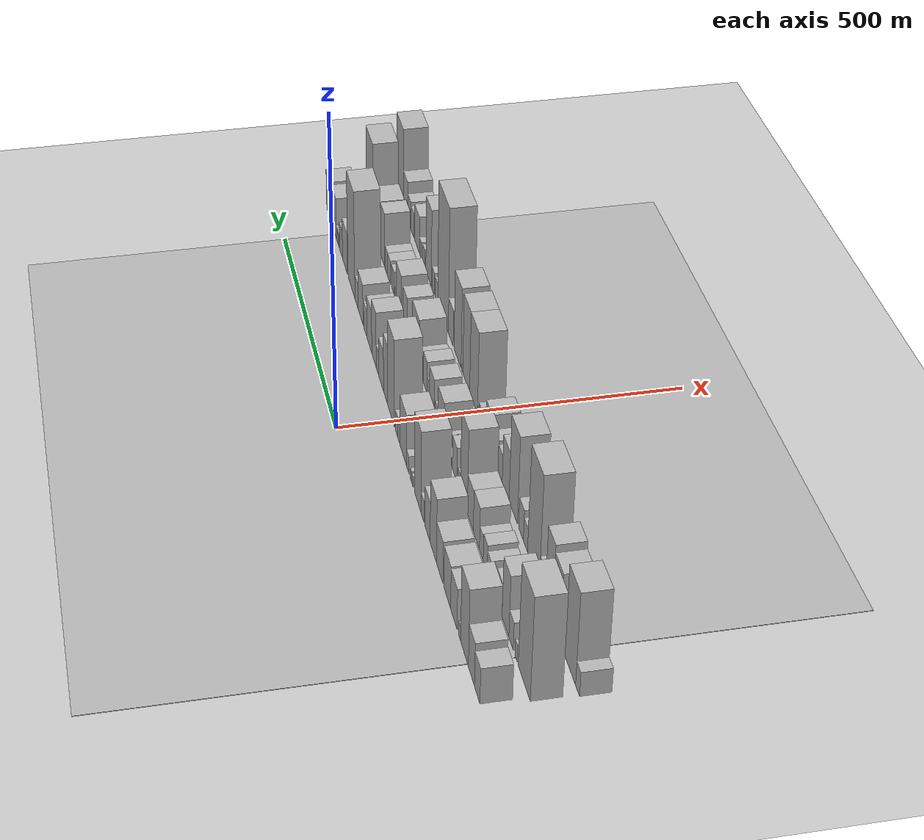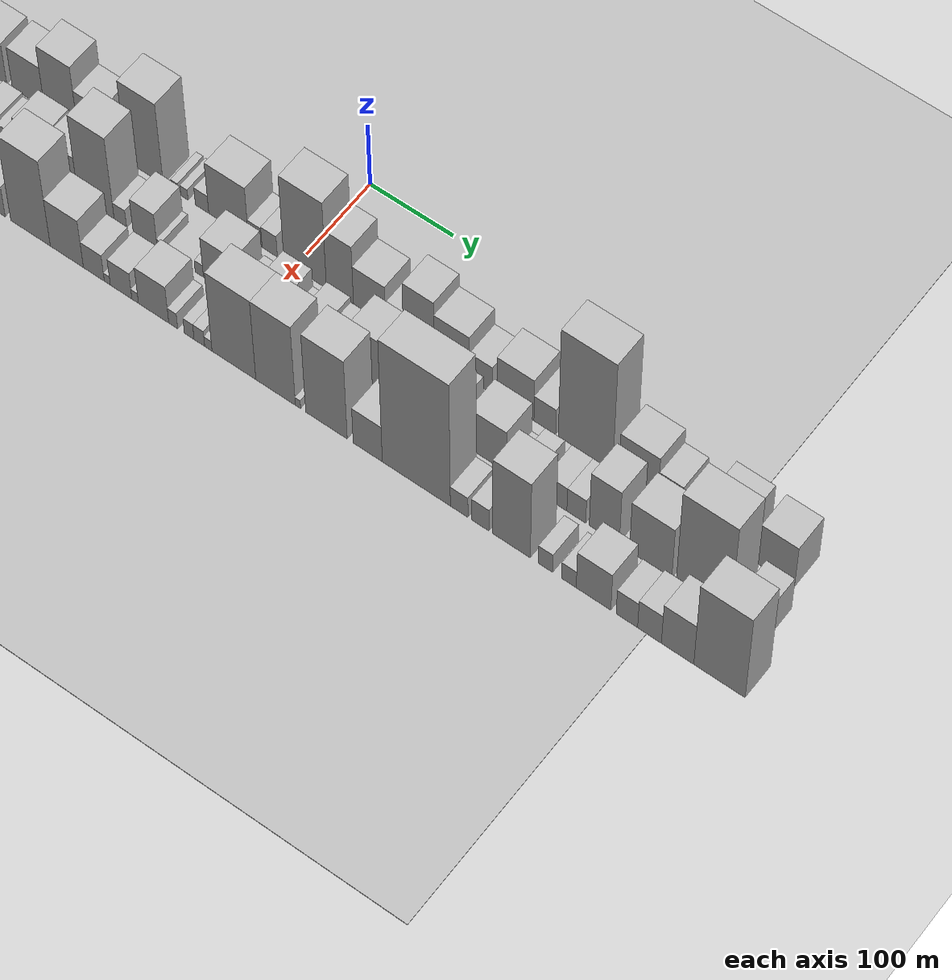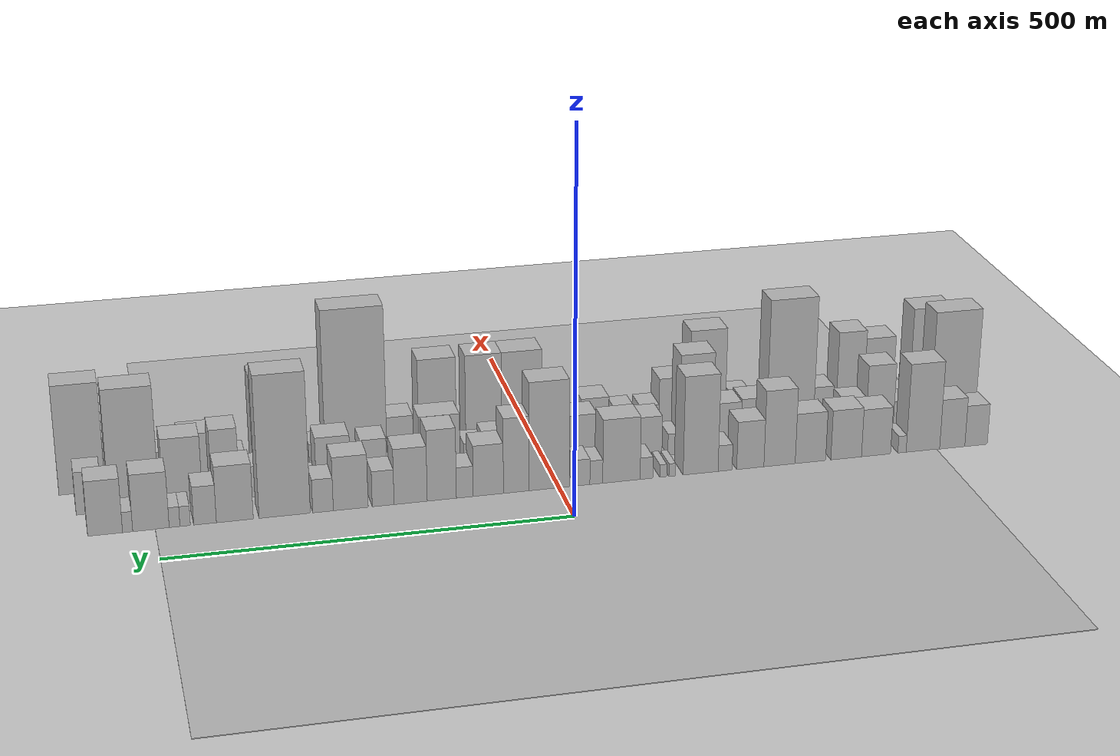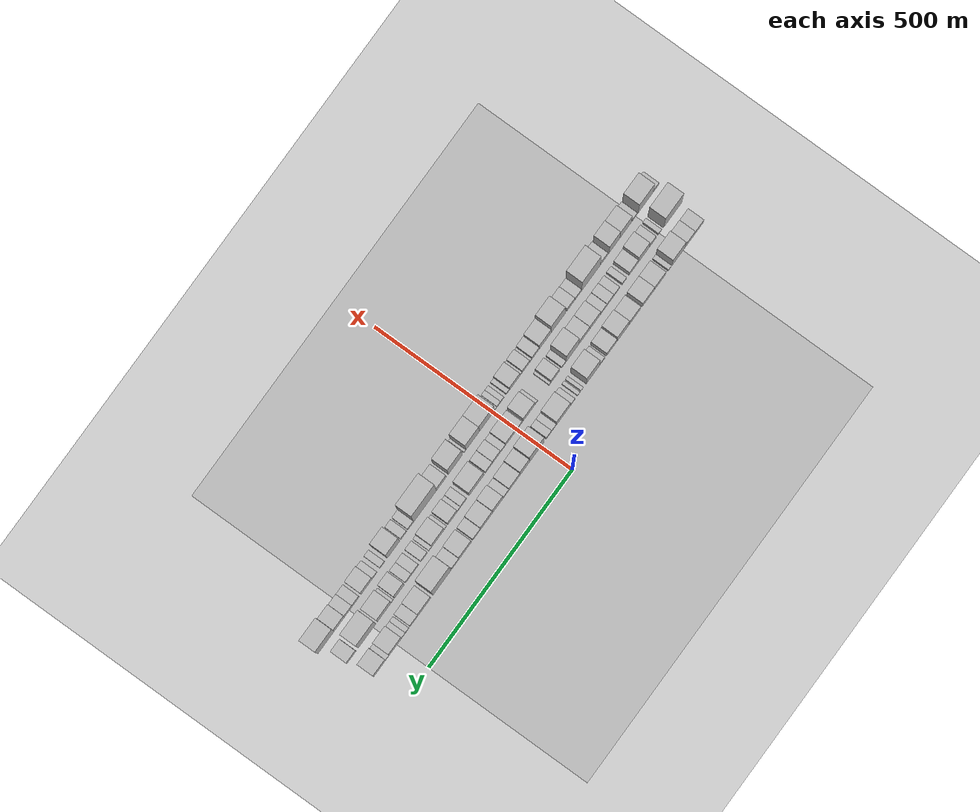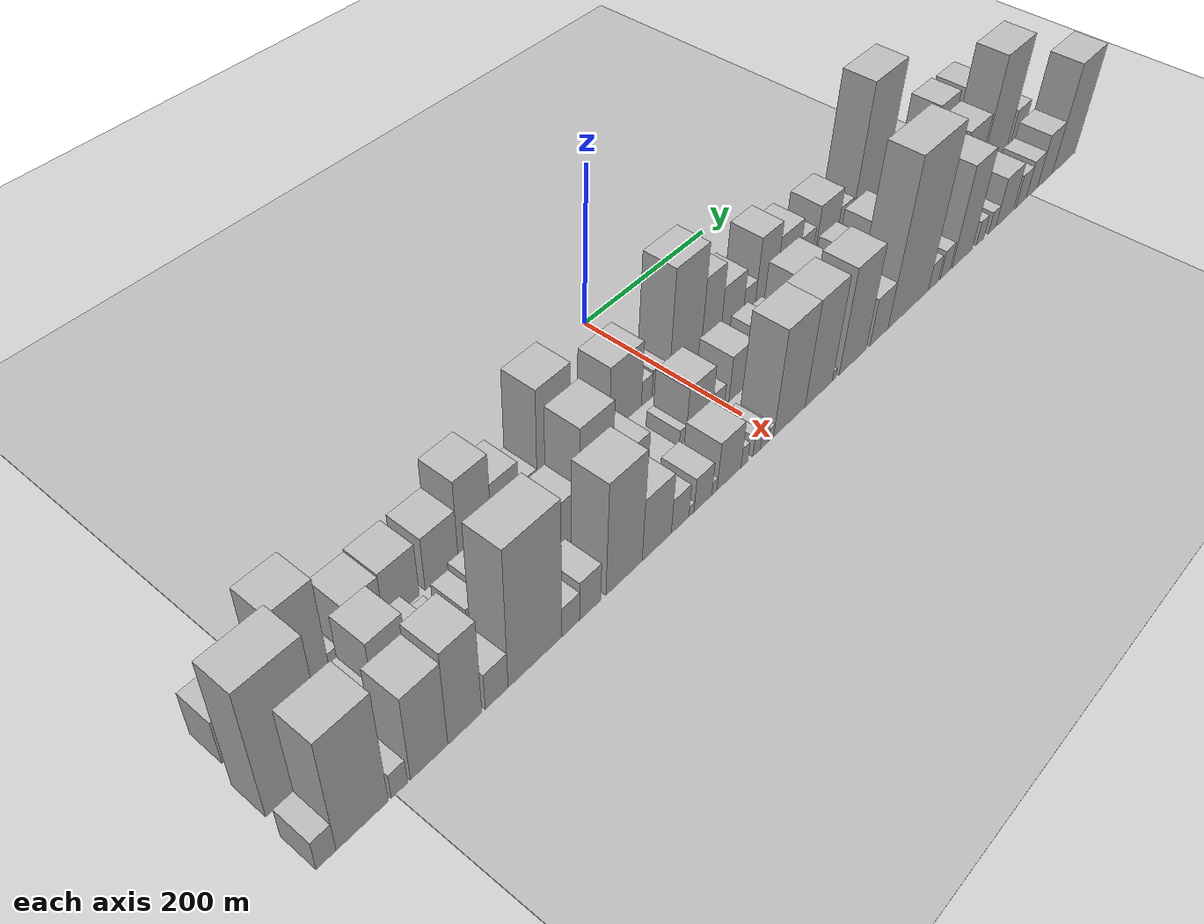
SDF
<?xml version="1.0" encoding="utf-8"?>

<sdf version="1.6">

   <world name="default">

      <gui fullscreen="0">

         <camera name="user_camera">

            <pose>-15 0 4.57585 0 0 0</pose>

            <view_controller>orbit</view_controller>

         </camera>

      </gui>

      <scene>

         <sky>

           <clouds>

             <speed>12</speed>

           </clouds>

         </sky>

         <ambient>0.4 0.4 0.4 1</ambient>

         <background>0.7 0.7 0.7 1</background>

         <shadows>1</shadows>

      </scene>

      <gravity>0 0 -9.8066</gravity>

      <magnetic_field>6e-06 2.3e-05 -4.2e-05</magnetic_field>

      <physics default="0" name="default_physics" type="ode">

         <ode>

            <solver>

               <type>quick</type>

               <iters>10</iters>

               <sor>1.0</sor>

               <use_dynamic_moi_rescaling>0</use_dynamic_moi_rescaling>

            </solver>

            <constraints>

               <cfm>0</cfm>

               <erp>0.2</erp>

               <contact_max_correcting_vel>100</contact_max_correcting_vel>

               <contact_surface_layer>0.001</contact_surface_layer>

            </constraints>

         </ode>

         <max_step_size>0.004</max_step_size>

         <real_time_factor>1</real_time_factor>

         <real_time_update_rate>250</real_time_update_rate>

      </physics>

      <light name="sun" type="directional">

         <cast_shadows>1</cast_shadows>

         <pose>0 0 10 0 0 0</pose>

         <diffuse>0.8 0.8 0.8 1</diffuse>

         <specular>0.2 0.2 0.2 1</specular>

         <attenuation>

            <range>1000</range>

            <constant>0.9</constant>

            <linear>0.01</linear>

            <quadratic>0.001</quadratic>

         </attenuation>

         <direction>-0.5 0.1 -0.9</direction>

      </light>

      <include>

         <name>ground_plane_1</name>

         <uri>model://HANNAS_ground_plane</uri>

         <pose>0 0 0  0 0 0</pose>

      </include>

      <include>

         <name>ground_plane_2</name>

         <uri>model://HANNAS_ground_plane</uri>

         <pose>100 0 0  0 0 0</pose>

      </include>

      <model name="building_1">

         <static>1</static>

         <pose frame="">100.0000 -554.4719 0 0.000000 0.000000 0.000000</pose>

         <link name="link">

            <pose frame="">0 0 28.50 0 0 0</pose>

            <collision name="collision">

               <geometry>

                  <box>

                     <size>40.0000 31.0561 57.0000</size>

                  </box>

               </geometry>

               <max_contacts>10</max_contacts>

               <surface>

                  <contact>

                     <ode/>

                  </contact>

                  <bounce/>

                  <friction>

                     <torsional>

                        <ode/>

                     </torsional>

                     <ode/>

                  </friction>

               </surface>

            </collision>

            <visual name="visual">

               <cast_shadows>0</cast_shadows>

               <geometry>

                  <box>

                     <size>40.0000 31.0561 57.0000</size>

                  </box>

               </geometry>

               <material>

                  <script>

                     <uri>model://HANNAS_wall/materials/scripts</uri>

                     <uri>model://HANNAS_wall/materials/textures</uri>

                     <name>vrc/HANNAS_wall</name>

                  </script>

               </material>

            </visual>

            <self_collide>0</self_collide>

            <enable_wind>0</enable_wind>

            <kinematic>0</kinematic>

         </link>

      </model>

      <model name="building_2">

         <static>1</static>

         <pose frame="">100.0000 -521.5871 0 0.000000 0.000000 0.000000</pose>

         <link name="link">

            <pose frame="">0 0 34.50 0 0 0</pose>

            <collision name="collision">

               <geometry>

                  <box>

                     <size>40.0000 34.7136 69.0000</size>

                  </box>

               </geometry>

               <max_contacts>10</max_contacts>

               <surface>

                  <contact>

                     <ode/>

                  </contact>

                  <bounce/>

                  <friction>

                     <torsional>

                        <ode/>

                     </torsional>

                     <ode/>

                  </friction>

               </surface>

            </collision>

            <visual name="visual">

               <cast_shadows>0</cast_shadows>

               <geometry>

                  <box>

                     <size>40.0000 34.7136 69.0000</size>

                  </box>

               </geometry>

               <material>

                  <script>

                     <uri>model://HANNAS_wall/materials/scripts</uri>

                     <uri>model://HANNAS_wall/materials/textures</uri>

                     <name>vrc/HANNAS_wall</name>

                  </script>

               </material>

            </visual>

            <self_collide>0</self_collide>

            <enable_wind>0</enable_wind>

            <kinematic>0</kinematic>

         </link>

      </model>

      <model name="building_3">

         <static>1</static>

         <pose frame="">100.0000 -481.3162 0 0.000000 0.000000 0.000000</pose>

         <link name="link">

            <pose frame="">0 0 61.50 0 0 0</pose>

            <collision name="collision">

               <geometry>

                  <box>

                     <size>40.0000 45.8280 123.0000</size>

                  </box>

               </geometry>

               <max_contacts>10</max_contacts>

               <surface>

                  <contact>

                     <ode/>

                  </contact>

                  <bounce/>

                  <friction>

                     <torsional>

                        <ode/>

                     </torsional>

                     <ode/>

                  </friction>

               </surface>

            </collision>

            <visual name="visual">

               <cast_shadows>0</cast_shadows>

               <geometry>

                  <box>

                     <size>40.0000 45.8280 123.0000</size>

                  </box>

               </geometry>

               <material>

                  <script>

                     <uri>model://HANNAS_wall/materials/scripts</uri>

                     <uri>model://HANNAS_wall/materials/textures</uri>

                     <name>vrc/HANNAS_wall</name>

                  </script>

               </material>

            </visual>

            <self_collide>0</self_collide>

            <enable_wind>0</enable_wind>

            <kinematic>0</kinematic>

         </link>

      </model>

      <model name="building_4">

         <static>1</static>

         <pose frame="">100.0000 -452.7569 0 0.000000 0.000000 0.000000</pose>

         <link name="link">

            <pose frame="">0 0 12.00 0 0 0</pose>

            <collision name="collision">

               <geometry>

                  <box>

                     <size>40.0000 11.2907 24.0000</size>

                  </box>

               </geometry>

               <max_contacts>10</max_contacts>

               <surface>

                  <contact>

                     <ode/>

                  </contact>

                  <bounce/>

                  <friction>

                     <torsional>

                        <ode/>

                     </torsional>

                     <ode/>

                  </friction>

               </surface>

            </collision>

            <visual name="visual">

               <cast_shadows>0</cast_shadows>

               <geometry>

                  <box>

                     <size>40.0000 11.2907 24.0000</size>

                  </box>

               </geometry>

               <material>

                  <script>

                     <uri>model://HANNAS_wall/materials/scripts</uri>

                     <uri>model://HANNAS_wall/materials/textures</uri>

                     <name>vrc/HANNAS_wall</name>

                  </script>

               </material>

            </visual>

            <self_collide>0</self_collide>

            <enable_wind>0</enable_wind>

            <kinematic>0</kinematic>

         </link>

      </model>

      <model name="building_5">

         <static>1</static>

         <pose frame="">100.0000 -417.3665 0 0.000000 0.000000 0.000000</pose>

         <link name="link">

            <pose frame="">0 0 33.00 0 0 0</pose>

            <collision name="collision">

               <geometry>

                  <box>

                     <size>40.0000 39.4901 66.0000</size>

                  </box>

               </geometry>

               <max_contacts>10</max_contacts>

               <surface>

                  <contact>

                     <ode/>

                  </contact>

                  <bounce/>

                  <friction>

                     <torsional>

                        <ode/>

                     </torsional>

                     <ode/>

                  </friction>

               </surface>

            </collision>

            <visual name="visual">

               <cast_shadows>0</cast_shadows>

               <geometry>

                  <box>

                     <size>40.0000 39.4901 66.0000</size>

                  </box>

               </geometry>

               <material>

                  <script>

                     <uri>model://HANNAS_wall/materials/scripts</uri>

                     <uri>model://HANNAS_wall/materials/textures</uri>

                     <name>vrc/HANNAS_wall</name>

                  </script>

               </material>

            </visual>

            <self_collide>0</self_collide>

            <enable_wind>0</enable_wind>

            <kinematic>0</kinematic>

         </link>

      </model>

      <model name="building_6">

         <static>1</static>

         <pose frame="">100.0000 -376.9387 0 0.000000 0.000000 0.000000</pose>

         <link name="link">

            <pose frame="">0 0 34.50 0 0 0</pose>

            <collision name="collision">

               <geometry>

                  <box>

                     <size>40.0000 41.3656 69.0000</size>

                  </box>

               </geometry>

               <max_contacts>10</max_contacts>

               <surface>

                  <contact>

                     <ode/>

                  </contact>

                  <bounce/>

                  <friction>

                     <torsional>

                        <ode/>

                     </torsional>

                     <ode/>

                  </friction>

               </surface>

            </collision>

            <visual name="visual">

               <cast_shadows>0</cast_shadows>

               <geometry>

                  <box>

                     <size>40.0000 41.3656 69.0000</size>

                  </box>

               </geometry>

               <material>

                  <script>

                     <uri>model://HANNAS_wall/materials/scripts</uri>

                     <uri>model://HANNAS_wall/materials/textures</uri>

                     <name>vrc/HANNAS_wall</name>

                  </script>

               </material>

            </visual>

            <self_collide>0</self_collide>

            <enable_wind>0</enable_wind>

            <kinematic>0</kinematic>

         </link>

      </model>

      <model name="building_7">

         <static>1</static>

         <pose frame="">100.0000 -328.8341 0 0.000000 0.000000 0.000000</pose>

         <link name="link">

            <pose frame="">0 0 34.50 0 0 0</pose>

            <collision name="collision">

               <geometry>

                  <box>

                     <size>40.0000 40.8436 69.0000</size>

                  </box>

               </geometry>

               <max_contacts>10</max_contacts>

               <surface>

                  <contact>

                     <ode/>

                  </contact>

                  <bounce/>

                  <friction>

                     <torsional>

                        <ode/>

                     </torsional>

                     <ode/>

                  </friction>

               </surface>

            </collision>

            <visual name="visual">

               <cast_shadows>0</cast_shadows>

               <geometry>

                  <box>

                     <size>40.0000 40.8436 69.0000</size>

                  </box>

               </geometry>

               <material>

                  <script>

                     <uri>model://HANNAS_wall/materials/scripts</uri>

                     <uri>model://HANNAS_wall/materials/textures</uri>

                     <name>vrc/HANNAS_wall</name>

                  </script>

               </material>

            </visual>

            <self_collide>0</self_collide>

            <enable_wind>0</enable_wind>

            <kinematic>0</kinematic>

         </link>

      </model>

      <model name="building_8">

         <static>1</static>

         <pose frame="">100.0000 -287.5396 0 0.000000 0.000000 0.000000</pose>

         <link name="link">

            <pose frame="">0 0 52.50 0 0 0</pose>

            <collision name="collision">

               <geometry>

                  <box>

                     <size>40.0000 41.7453 105.0000</size>

                  </box>

               </geometry>

               <max_contacts>10</max_contacts>

               <surface>

                  <contact>

                     <ode/>

                  </contact>

                  <bounce/>

                  <friction>

                     <torsional>

                        <ode/>

                     </torsional>

                     <ode/>

                  </friction>

               </surface>

            </collision>

            <visual name="visual">

               <cast_shadows>0</cast_shadows>

               <geometry>

                  <box>

                     <size>40.0000 41.7453 105.0000</size>

                  </box>

               </geometry>

               <material>

                  <script>

                     <uri>model://HANNAS_wall/materials/scripts</uri>

                     <uri>model://HANNAS_wall/materials/textures</uri>

                     <name>vrc/HANNAS_wall</name>

                  </script>

               </material>

            </visual>

            <self_collide>0</self_collide>

            <enable_wind>0</enable_wind>

            <kinematic>0</kinematic>

         </link>

      </model>

      <model name="building_9">

         <static>1</static>

         <pose frame="">100.0000 -248.6137 0 0.000000 0.000000 0.000000</pose>

         <link name="link">

            <pose frame="">0 0 33.00 0 0 0</pose>

            <collision name="collision">

               <geometry>

                  <box>

                     <size>40.0000 36.1065 66.0000</size>

                  </box>

               </geometry>

               <max_contacts>10</max_contacts>

               <surface>

                  <contact>

                     <ode/>

                  </contact>

                  <bounce/>

                  <friction>

                     <torsional>

                        <ode/>

                     </torsional>

                     <ode/>

                  </friction>

               </surface>

            </collision>

            <visual name="visual">

               <cast_shadows>0</cast_shadows>

               <geometry>

                  <box>

                     <size>40.0000 36.1065 66.0000</size>

                  </box>

               </geometry>

               <material>

                  <script>

                     <uri>model://HANNAS_wall/materials/scripts</uri>

                     <uri>model://HANNAS_wall/materials/textures</uri>

                     <name>vrc/HANNAS_wall</name>

                  </script>

               </material>

            </visual>

            <self_collide>0</self_collide>

            <enable_wind>0</enable_wind>

            <kinematic>0</kinematic>

         </link>

      </model>

      <model name="building_10">

         <static>1</static>

         <pose frame="">100.0000 -215.2584 0 0.000000 0.000000 0.000000</pose>

         <link name="link">

            <pose frame="">0 0 18.00 0 0 0</pose>

            <collision name="collision">

               <geometry>

                  <box>

                     <size>40.0000 18.6041 36.0000</size>

                  </box>

               </geometry>

               <max_contacts>10</max_contacts>

               <surface>

                  <contact>

                     <ode/>

                  </contact>

                  <bounce/>

                  <friction>

                     <torsional>

                        <ode/>

                     </torsional>

                     <ode/>

                  </friction>

               </surface>

            </collision>

            <visual name="visual">

               <cast_shadows>0</cast_shadows>

               <geometry>

                  <box>

                     <size>40.0000 18.6041 36.0000</size>

                  </box>

               </geometry>

               <material>

                  <script>

                     <uri>model://HANNAS_wall/materials/scripts</uri>

                     <uri>model://HANNAS_wall/materials/textures</uri>

                     <name>vrc/HANNAS_wall</name>

                  </script>

               </material>

            </visual>

            <self_collide>0</self_collide>

            <enable_wind>0</enable_wind>

            <kinematic>0</kinematic>

         </link>

      </model>

      <model name="building_11">

         <static>1</static>

         <pose frame="">100.0000 -183.0226 0 0.000000 0.000000 0.000000</pose>

         <link name="link">

            <pose frame="">0 0 67.50 0 0 0</pose>

            <collision name="collision">

               <geometry>

                  <box>

                     <size>40.0000 45.8675 135.0000</size>

                  </box>

               </geometry>

               <max_contacts>10</max_contacts>

               <surface>

                  <contact>

                     <ode/>

                  </contact>

                  <bounce/>

                  <friction>

                     <torsional>

                        <ode/>

                     </torsional>

                     <ode/>

                  </friction>

               </surface>

            </collision>

            <visual name="visual">

               <cast_shadows>0</cast_shadows>

               <geometry>

                  <box>

                     <size>40.0000 45.8675 135.0000</size>

                  </box>

               </geometry>

               <material>

                  <script>

                     <uri>model://HANNAS_wall/materials/scripts</uri>

                     <uri>model://HANNAS_wall/materials/textures</uri>

                     <name>vrc/HANNAS_wall</name>

                  </script>

               </material>

            </visual>

            <self_collide>0</self_collide>

            <enable_wind>0</enable_wind>

            <kinematic>0</kinematic>

         </link>

      </model>

      <model name="building_12">

         <static>1</static>

         <pose frame="">100.0000 -145.7582 0 0.000000 0.000000 0.000000</pose>

         <link name="link">

            <pose frame="">0 0 9.00 0 0 0</pose>

            <collision name="collision">

               <geometry>

                  <box>

                     <size>40.0000 8.6613 18.0000</size>

                  </box>

               </geometry>

               <max_contacts>10</max_contacts>

               <surface>

                  <contact>

                     <ode/>

                  </contact>

                  <bounce/>

                  <friction>

                     <torsional>

                        <ode/>

                     </torsional>

                     <ode/>

                  </friction>

               </surface>

            </collision>

            <visual name="visual">

               <cast_shadows>0</cast_shadows>

               <geometry>

                  <box>

                     <size>40.0000 8.6613 18.0000</size>

                  </box>

               </geometry>

               <material>

                  <script>

                     <uri>model://HANNAS_wall/materials/scripts</uri>

                     <uri>model://HANNAS_wall/materials/textures</uri>

                     <name>vrc/HANNAS_wall</name>

                  </script>

               </material>

            </visual>

            <self_collide>0</self_collide>

            <enable_wind>0</enable_wind>

            <kinematic>0</kinematic>

         </link>

      </model>

      <model name="building_13">

         <static>1</static>

         <pose frame="">100.0000 -133.9505 0 0.000000 0.000000 0.000000</pose>

         <link name="link">

            <pose frame="">0 0 9.00 0 0 0</pose>

            <collision name="collision">

               <geometry>

                  <box>

                     <size>40.0000 8.9541 18.0000</size>

                  </box>

               </geometry>

               <max_contacts>10</max_contacts>

               <surface>

                  <contact>

                     <ode/>

                  </contact>

                  <bounce/>

                  <friction>

                     <torsional>

                        <ode/>

                     </torsional>

                     <ode/>

                  </friction>

               </surface>

            </collision>

            <visual name="visual">

               <cast_shadows>0</cast_shadows>

               <geometry>

                  <box>

                     <size>40.0000 8.9541 18.0000</size>

                  </box>

               </geometry>

               <material>

                  <script>

                     <uri>model://HANNAS_wall/materials/scripts</uri>

                     <uri>model://HANNAS_wall/materials/textures</uri>

                     <name>vrc/HANNAS_wall</name>

                  </script>

               </material>

            </visual>

            <self_collide>0</self_collide>

            <enable_wind>0</enable_wind>

            <kinematic>0</kinematic>

         </link>

      </model>

      <model name="building_14">

         <static>1</static>

         <pose frame="">100.0000 -112.2183 0 0.000000 0.000000 0.000000</pose>

         <link name="link">

            <pose frame="">0 0 15.00 0 0 0</pose>

            <collision name="collision">

               <geometry>

                  <box>

                     <size>40.0000 16.5102 30.0000</size>

                  </box>

               </geometry>

               <max_contacts>10</max_contacts>

               <surface>

                  <contact>

                     <ode/>

                  </contact>

                  <bounce/>

                  <friction>

                     <torsional>

                        <ode/>

                     </torsional>

                     <ode/>

                  </friction>

               </surface>

            </collision>

            <visual name="visual">

               <cast_shadows>0</cast_shadows>

               <geometry>

                  <box>

                     <size>40.0000 16.5102 30.0000</size>

                  </box>

               </geometry>

               <material>

                  <script>

                     <uri>model://HANNAS_wall/materials/scripts</uri>

                     <uri>model://HANNAS_wall/materials/textures</uri>

                     <name>vrc/HANNAS_wall</name>

                  </script>

               </material>

            </visual>

            <self_collide>0</self_collide>

            <enable_wind>0</enable_wind>

            <kinematic>0</kinematic>

         </link>

      </model>

      <model name="building_15">

         <static>1</static>

         <pose frame="">100.0000 -79.7045 0 0.000000 0.000000 0.000000</pose>

         <link name="link">

            <pose frame="">0 0 43.50 0 0 0</pose>

            <collision name="collision">

               <geometry>

                  <box>

                     <size>40.0000 48.5175 87.0000</size>

                  </box>

               </geometry>

               <max_contacts>10</max_contacts>

               <surface>

                  <contact>

                     <ode/>

                  </contact>

                  <bounce/>

                  <friction>

                     <torsional>

                        <ode/>

                     </torsional>

                     <ode/>

                  </friction>

               </surface>

            </collision>

            <visual name="visual">

               <cast_shadows>0</cast_shadows>

               <geometry>

                  <box>

                     <size>40.0000 48.5175 87.0000</size>

                  </box>

               </geometry>

               <material>

                  <script>

                     <uri>model://HANNAS_wall/materials/scripts</uri>

                     <uri>model://HANNAS_wall/materials/textures</uri>

                     <name>vrc/HANNAS_wall</name>

                  </script>

               </material>

            </visual>

            <self_collide>0</self_collide>

            <enable_wind>0</enable_wind>

            <kinematic>0</kinematic>

         </link>

      </model>

      <model name="building_16">

         <static>1</static>

         <pose frame="">100.0000 -47.1491 0 0.000000 0.000000 0.000000</pose>

         <link name="link">

            <pose frame="">0 0 16.50 0 0 0</pose>

            <collision name="collision">

               <geometry>

                  <box>

                     <size>40.0000 16.5933 33.0000</size>

                  </box>

               </geometry>

               <max_contacts>10</max_contacts>

               <surface>

                  <contact>

                     <ode/>

                  </contact>

                  <bounce/>

                  <friction>

                     <torsional>

                        <ode/>

                     </torsional>

                     <ode/>

                  </friction>

               </surface>

            </collision>

            <visual name="visual">

               <cast_shadows>0</cast_shadows>

               <geometry>

                  <box>

                     <size>40.0000 16.5933 33.0000</size>

                  </box>

               </geometry>

               <material>

                  <script>

                     <uri>model://HANNAS_wall/materials/scripts</uri>

                     <uri>model://HANNAS_wall/materials/textures</uri>

                     <name>vrc/HANNAS_wall</name>

                  </script>

               </material>

            </visual>

            <self_collide>0</self_collide>

            <enable_wind>0</enable_wind>

            <kinematic>0</kinematic>

         </link>

      </model>

      <model name="building_17">

         <static>1</static>

         <pose frame="">100.0000 -29.5650 0 0.000000 0.000000 0.000000</pose>

         <link name="link">

            <pose frame="">0 0 18.00 0 0 0</pose>

            <collision name="collision">

               <geometry>

                  <box>

                     <size>40.0000 18.5749 36.0000</size>

                  </box>

               </geometry>

               <max_contacts>10</max_contacts>

               <surface>

                  <contact>

                     <ode/>

                  </contact>

                  <bounce/>

                  <friction>

                     <torsional>

                        <ode/>

                     </torsional>

                     <ode/>

                  </friction>

               </surface>

            </collision>

            <visual name="visual">

               <cast_shadows>0</cast_shadows>

               <geometry>

                  <box>

                     <size>40.0000 18.5749 36.0000</size>

                  </box>

               </geometry>

               <material>

                  <script>

                     <uri>model://HANNAS_wall/materials/scripts</uri>

                     <uri>model://HANNAS_wall/materials/textures</uri>

                     <name>vrc/HANNAS_wall</name>

                  </script>

               </material>

            </visual>

            <self_collide>0</self_collide>

            <enable_wind>0</enable_wind>

            <kinematic>0</kinematic>

         </link>

      </model>

      <model name="building_18">

         <static>1</static>

         <pose frame="">100.0000 13.3755 0 0.000000 0.000000 0.000000</pose>

         <link name="link">

            <pose frame="">0 0 73.50 0 0 0</pose>

            <collision name="collision">

               <geometry>

                  <box>

                     <size>40.0000 51.3061 147.0000</size>

                  </box>

               </geometry>

               <max_contacts>10</max_contacts>

               <surface>

                  <contact>

                     <ode/>

                  </contact>

                  <bounce/>

                  <friction>

                     <torsional>

                        <ode/>

                     </torsional>

                     <ode/>

                  </friction>

               </surface>

            </collision>

            <visual name="visual">

               <cast_shadows>0</cast_shadows>

               <geometry>

                  <box>

                     <size>40.0000 51.3061 147.0000</size>

                  </box>

               </geometry>

               <material>

                  <script>

                     <uri>model://HANNAS_wall/materials/scripts</uri>

                     <uri>model://HANNAS_wall/materials/textures</uri>

                     <name>vrc/HANNAS_wall</name>

                  </script>

               </material>

            </visual>

            <self_collide>0</self_collide>

            <enable_wind>0</enable_wind>

            <kinematic>0</kinematic>

         </link>

      </model>

      <model name="building_19">

         <static>1</static>

         <pose frame="">100.0000 55.3227 0 0.000000 0.000000 0.000000</pose>

         <link name="link">

            <pose frame="">0 0 51.00 0 0 0</pose>

            <collision name="collision">

               <geometry>

                  <box>

                     <size>40.0000 32.5883 102.0000</size>

                  </box>

               </geometry>

               <max_contacts>10</max_contacts>

               <surface>

                  <contact>

                     <ode/>

                  </contact>

                  <bounce/>

                  <friction>

                     <torsional>

                        <ode/>

                     </torsional>

                     <ode/>

                  </friction>

               </surface>

            </collision>

            <visual name="visual">

               <cast_shadows>0</cast_shadows>

               <geometry>

                  <box>

                     <size>40.0000 32.5883 102.0000</size>

                  </box>

               </geometry>

               <material>

                  <script>

                     <uri>model://HANNAS_wall/materials/scripts</uri>

                     <uri>model://HANNAS_wall/materials/textures</uri>

                     <name>vrc/HANNAS_wall</name>

                  </script>

               </material>

            </visual>

            <self_collide>0</self_collide>

            <enable_wind>0</enable_wind>

            <kinematic>0</kinematic>

         </link>

      </model>

      <model name="building_20">

         <static>1</static>

         <pose frame="">100.0000 90.7704 0 0.000000 0.000000 0.000000</pose>

         <link name="link">

            <pose frame="">0 0 34.50 0 0 0</pose>

            <collision name="collision">

               <geometry>

                  <box>

                     <size>40.0000 38.3070 69.0000</size>

                  </box>

               </geometry>

               <max_contacts>10</max_contacts>

               <surface>

                  <contact>

                     <ode/>

                  </contact>

                  <bounce/>

                  <friction>

                     <torsional>

                        <ode/>

                     </torsional>

                     <ode/>

                  </friction>

               </surface>

            </collision>

            <visual name="visual">

               <cast_shadows>0</cast_shadows>

               <geometry>

                  <box>

                     <size>40.0000 38.3070 69.0000</size>

                  </box>

               </geometry>

               <material>

                  <script>

                     <uri>model://HANNAS_wall/materials/scripts</uri>

                     <uri>model://HANNAS_wall/materials/textures</uri>

                     <name>vrc/HANNAS_wall</name>

                  </script>

               </material>

            </visual>

            <self_collide>0</self_collide>

            <enable_wind>0</enable_wind>

            <kinematic>0</kinematic>

         </link>

      </model>

      <model name="building_21">

         <static>1</static>

         <pose frame="">100.0000 120.4790 0 0.000000 0.000000 0.000000</pose>

         <link name="link">

            <pose frame="">0 0 21.00 0 0 0</pose>

            <collision name="collision">

               <geometry>

                  <box>

                     <size>40.0000 21.1102 42.0000</size>

                  </box>

               </geometry>

               <max_contacts>10</max_contacts>

               <surface>

                  <contact>

                     <ode/>

                  </contact>

                  <bounce/>

                  <friction>

                     <torsional>

                        <ode/>

                     </torsional>

                     <ode/>

                  </friction>

               </surface>

            </collision>

            <visual name="visual">

               <cast_shadows>0</cast_shadows>

               <geometry>

                  <box>

                     <size>40.0000 21.1102 42.0000</size>

                  </box>

               </geometry>

               <material>

                  <script>

                     <uri>model://HANNAS_wall/materials/scripts</uri>

                     <uri>model://HANNAS_wall/materials/textures</uri>

                     <name>vrc/HANNAS_wall</name>

                  </script>

               </material>

            </visual>

            <self_collide>0</self_collide>

            <enable_wind>0</enable_wind>

            <kinematic>0</kinematic>

         </link>

      </model>

      <model name="building_22">

         <static>1</static>

         <pose frame="">100.0000 149.3170 0 0.000000 0.000000 0.000000</pose>

         <link name="link">

            <pose frame="">0 0 48.00 0 0 0</pose>

            <collision name="collision">

               <geometry>

                  <box>

                     <size>40.0000 36.5658 96.0000</size>

                  </box>

               </geometry>

               <max_contacts>10</max_contacts>

               <surface>

                  <contact>

                     <ode/>

                  </contact>

                  <bounce/>

                  <friction>

                     <torsional>

                        <ode/>

                     </torsional>

                     <ode/>

                  </friction>

               </surface>

            </collision>

            <visual name="visual">

               <cast_shadows>0</cast_shadows>

               <geometry>

                  <box>

                     <size>40.0000 36.5658 96.0000</size>

                  </box>

               </geometry>

               <material>

                  <script>

                     <uri>model://HANNAS_wall/materials/scripts</uri>

                     <uri>model://HANNAS_wall/materials/textures</uri>

                     <name>vrc/HANNAS_wall</name>

                  </script>

               </material>

            </visual>

            <self_collide>0</self_collide>

            <enable_wind>0</enable_wind>

            <kinematic>0</kinematic>

         </link>

      </model>

      <model name="building_23">

         <static>1</static>

         <pose frame="">100.0000 188.3108 0 0.000000 0.000000 0.000000</pose>

         <link name="link">

            <pose frame="">0 0 37.50 0 0 0</pose>

            <collision name="collision">

               <geometry>

                  <box>

                     <size>40.0000 41.4217 75.0000</size>

                  </box>

               </geometry>

               <max_contacts>10</max_contacts>

               <surface>

                  <contact>

                     <ode/>

                  </contact>

                  <bounce/>

                  <friction>

                     <torsional>

                        <ode/>

                     </torsional>

                     <ode/>

                  </friction>

               </surface>

            </collision>

            <visual name="visual">

               <cast_shadows>0</cast_shadows>

               <geometry>

                  <box>

                     <size>40.0000 41.4217 75.0000</size>

                  </box>

               </geometry>

               <material>

                  <script>

                     <uri>model://HANNAS_wall/materials/scripts</uri>

                     <uri>model://HANNAS_wall/materials/textures</uri>

                     <name>vrc/HANNAS_wall</name>

                  </script>

               </material>

            </visual>

            <self_collide>0</self_collide>

            <enable_wind>0</enable_wind>

            <kinematic>0</kinematic>

         </link>

      </model>

      <model name="building_24">

         <static>1</static>

         <pose frame="">100.0000 222.5513 0 0.000000 0.000000 0.000000</pose>

         <link name="link">

            <pose frame="">0 0 24.00 0 0 0</pose>

            <collision name="collision">

               <geometry>

                  <box>

                     <size>40.0000 27.0594 48.0000</size>

                  </box>

               </geometry>

               <max_contacts>10</max_contacts>

               <surface>

                  <contact>

                     <ode/>

                  </contact>

                  <bounce/>

                  <friction>

                     <torsional>

                        <ode/>

                     </torsional>

                     <ode/>

                  </friction>

               </surface>

            </collision>

            <visual name="visual">

               <cast_shadows>0</cast_shadows>

               <geometry>

                  <box>

                     <size>40.0000 27.0594 48.0000</size>

                  </box>

               </geometry>

               <material>

                  <script>

                     <uri>model://HANNAS_wall/materials/scripts</uri>

                     <uri>model://HANNAS_wall/materials/textures</uri>

                     <name>vrc/HANNAS_wall</name>

                  </script>

               </material>

            </visual>

            <self_collide>0</self_collide>

            <enable_wind>0</enable_wind>

            <kinematic>0</kinematic>

         </link>

      </model>

      <model name="building_25">

         <static>1</static>

         <pose frame="">100.0000 262.6222 0 0.000000 0.000000 0.000000</pose>

         <link name="link">

            <pose frame="">0 0 36.00 0 0 0</pose>

            <collision name="collision">

               <geometry>

                  <box>

                     <size>40.0000 43.0822 72.0000</size>

                  </box>

               </geometry>

               <max_contacts>10</max_contacts>

               <surface>

                  <contact>

                     <ode/>

                  </contact>

                  <bounce/>

                  <friction>

                     <torsional>

                        <ode/>

                     </torsional>

                     <ode/>

                  </friction>

               </surface>

            </collision>

            <visual name="visual">

               <cast_shadows>0</cast_shadows>

               <geometry>

                  <box>

                     <size>40.0000 43.0822 72.0000</size>

                  </box>

               </geometry>

               <material>

                  <script>

                     <uri>model://HANNAS_wall/materials/scripts</uri>

                     <uri>model://HANNAS_wall/materials/textures</uri>

                     <name>vrc/HANNAS_wall</name>

                  </script>

               </material>

            </visual>

            <self_collide>0</self_collide>

            <enable_wind>0</enable_wind>

            <kinematic>0</kinematic>

         </link>

      </model>

      <model name="building_26">

         <static>1</static>

         <pose frame="">100.0000 296.7847 0 0.000000 0.000000 0.000000</pose>

         <link name="link">

            <pose frame="">0 0 22.50 0 0 0</pose>

            <collision name="collision">

               <geometry>

                  <box>

                     <size>40.0000 25.2428 45.0000</size>

                  </box>

               </geometry>

               <max_contacts>10</max_contacts>

               <surface>

                  <contact>

                     <ode/>

                  </contact>

                  <bounce/>

                  <friction>

                     <torsional>

                        <ode/>

                     </torsional>

                     <ode/>

                  </friction>

               </surface>

            </collision>

            <visual name="visual">

               <cast_shadows>0</cast_shadows>

               <geometry>

                  <box>

                     <size>40.0000 25.2428 45.0000</size>

                  </box>

               </geometry>

               <material>

                  <script>

                     <uri>model://HANNAS_wall/materials/scripts</uri>

                     <uri>model://HANNAS_wall/materials/textures</uri>

                     <name>vrc/HANNAS_wall</name>

                  </script>

               </material>

            </visual>

            <self_collide>0</self_collide>

            <enable_wind>0</enable_wind>

            <kinematic>0</kinematic>

         </link>

      </model>

      <model name="building_27">

         <static>1</static>

         <pose frame="">100.0000 343.6856 0 0.000000 0.000000 0.000000</pose>

         <link name="link">

            <pose frame="">0 0 94.50 0 0 0</pose>

            <collision name="collision">

               <geometry>

                  <box>

                     <size>40.0000 62.5591 189.0000</size>

                  </box>

               </geometry>

               <max_contacts>10</max_contacts>

               <surface>

                  <contact>

                     <ode/>

                  </contact>

                  <bounce/>

                  <friction>

                     <torsional>

                        <ode/>

                     </torsional>

                     <ode/>

                  </friction>

               </surface>

            </collision>

            <visual name="visual">

               <cast_shadows>0</cast_shadows>

               <geometry>

                  <box>

                     <size>40.0000 62.5591 189.0000</size>

                  </box>

               </geometry>

               <material>

                  <script>

                     <uri>model://HANNAS_wall/materials/scripts</uri>

                     <uri>model://HANNAS_wall/materials/textures</uri>

                     <name>vrc/HANNAS_wall</name>

                  </script>

               </material>

            </visual>

            <self_collide>0</self_collide>

            <enable_wind>0</enable_wind>

            <kinematic>0</kinematic>

         </link>

      </model>

      <model name="building_28">

         <static>1</static>

         <pose frame="">100.0000 404.2850 0 0.000000 0.000000 0.000000</pose>

         <link name="link">

            <pose frame="">0 0 37.50 0 0 0</pose>

            <collision name="collision">

               <geometry>

                  <box>

                     <size>40.0000 44.6396 75.0000</size>

                  </box>

               </geometry>

               <max_contacts>10</max_contacts>

               <surface>

                  <contact>

                     <ode/>

                  </contact>

                  <bounce/>

                  <friction>

                     <torsional>

                        <ode/>

                     </torsional>

                     <ode/>

                  </friction>

               </surface>

            </collision>

            <visual name="visual">

               <cast_shadows>0</cast_shadows>

               <geometry>

                  <box>

                     <size>40.0000 44.6396 75.0000</size>

                  </box>

               </geometry>

               <material>

                  <script>

                     <uri>model://HANNAS_wall/materials/scripts</uri>

                     <uri>model://HANNAS_wall/materials/textures</uri>

                     <name>vrc/HANNAS_wall</name>

                  </script>

               </material>

            </visual>

            <self_collide>0</self_collide>

            <enable_wind>0</enable_wind>

            <kinematic>0</kinematic>

         </link>

      </model>

      <model name="building_29">

         <static>1</static>

         <pose frame="">100.0000 440.2491 0 0.000000 0.000000 0.000000</pose>

         <link name="link">

            <pose frame="">0 0 25.50 0 0 0</pose>

            <collision name="collision">

               <geometry>

                  <box>

                     <size>40.0000 27.2887 51.0000</size>

                  </box>

               </geometry>

               <max_contacts>10</max_contacts>

               <surface>

                  <contact>

                     <ode/>

                  </contact>

                  <bounce/>

                  <friction>

                     <torsional>

                        <ode/>

                     </torsional>

                     <ode/>

                  </friction>

               </surface>

            </collision>

            <visual name="visual">

               <cast_shadows>0</cast_shadows>

               <geometry>

                  <box>

                     <size>40.0000 27.2887 51.0000</size>

                  </box>

               </geometry>

               <material>

                  <script>

                     <uri>model://HANNAS_wall/materials/scripts</uri>

                     <uri>model://HANNAS_wall/materials/textures</uri>

                     <name>vrc/HANNAS_wall</name>

                  </script>

               </material>

            </visual>

            <self_collide>0</self_collide>

            <enable_wind>0</enable_wind>

            <kinematic>0</kinematic>

         </link>

      </model>

      <model name="building_30">

         <static>1</static>

         <pose frame="">100.0000 464.1516 0 0.000000 0.000000 0.000000</pose>

         <link name="link">

            <pose frame="">0 0 13.50 0 0 0</pose>

            <collision name="collision">

               <geometry>

                  <box>

                     <size>40.0000 12.5163 27.0000</size>

                  </box>

               </geometry>

               <max_contacts>10</max_contacts>

               <surface>

                  <contact>

                     <ode/>

                  </contact>

                  <bounce/>

                  <friction>

                     <torsional>

                        <ode/>

                     </torsional>

                     <ode/>

                  </friction>

               </surface>

            </collision>

            <visual name="visual">

               <cast_shadows>0</cast_shadows>

               <geometry>

                  <box>

                     <size>40.0000 12.5163 27.0000</size>

                  </box>

               </geometry>

               <material>

                  <script>

                     <uri>model://HANNAS_wall/materials/scripts</uri>

                     <uri>model://HANNAS_wall/materials/textures</uri>

                     <name>vrc/HANNAS_wall</name>

                  </script>

               </material>

            </visual>

            <self_collide>0</self_collide>

            <enable_wind>0</enable_wind>

            <kinematic>0</kinematic>

         </link>

      </model>

      <model name="building_31">

         <static>1</static>

         <pose frame="">100.0000 476.8424 0 0.000000 0.000000 0.000000</pose>

         <link name="link">

            <pose frame="">0 0 13.50 0 0 0</pose>

            <collision name="collision">

               <geometry>

                  <box>

                     <size>40.0000 12.8654 27.0000</size>

                  </box>

               </geometry>

               <max_contacts>10</max_contacts>

               <surface>

                  <contact>

                     <ode/>

                  </contact>

                  <bounce/>

                  <friction>

                     <torsional>

                        <ode/>

                     </torsional>

                     <ode/>

                  </friction>

               </surface>

            </collision>

            <visual name="visual">

               <cast_shadows>0</cast_shadows>

               <geometry>

                  <box>

                     <size>40.0000 12.8654 27.0000</size>

                  </box>

               </geometry>

               <material>

                  <script>

                     <uri>model://HANNAS_wall/materials/scripts</uri>

                     <uri>model://HANNAS_wall/materials/textures</uri>

                     <name>vrc/HANNAS_wall</name>

                  </script>

               </material>

            </visual>

            <self_collide>0</self_collide>

            <enable_wind>0</enable_wind>

            <kinematic>0</kinematic>

         </link>

      </model>

      <model name="building_32">

         <static>1</static>

         <pose frame="">100.0000 505.0232 0 0.000000 0.000000 0.000000</pose>

         <link name="link">

            <pose frame="">0 0 37.50 0 0 0</pose>

            <collision name="collision">

               <geometry>

                  <box>

                     <size>40.0000 43.4962 75.0000</size>

                  </box>

               </geometry>

               <max_contacts>10</max_contacts>

               <surface>

                  <contact>

                     <ode/>

                  </contact>

                  <bounce/>

                  <friction>

                     <torsional>

                        <ode/>

                     </torsional>

                     <ode/>

                  </friction>

               </surface>

            </collision>

            <visual name="visual">

               <cast_shadows>0</cast_shadows>

               <geometry>

                  <box>

                     <size>40.0000 43.4962 75.0000</size>

                  </box>

               </geometry>

               <material>

                  <script>

                     <uri>model://HANNAS_wall/materials/scripts</uri>

                     <uri>model://HANNAS_wall/materials/textures</uri>

                     <name>vrc/HANNAS_wall</name>

                  </script>

               </material>

            </visual>

            <self_collide>0</self_collide>

            <enable_wind>0</enable_wind>

            <kinematic>0</kinematic>

         </link>

      </model>

      <model name="building_33">

         <static>1</static>

         <pose frame="">100.0000 532.8068 0 0.000000 0.000000 0.000000</pose>

         <link name="link">

            <pose frame="">0 0 13.50 0 0 0</pose>

            <collision name="collision">

               <geometry>

                  <box>

                     <size>40.0000 12.0710 27.0000</size>

                  </box>

               </geometry>

               <max_contacts>10</max_contacts>

               <surface>

                  <contact>

                     <ode/>

                  </contact>

                  <bounce/>

                  <friction>

                     <torsional>

                        <ode/>

                     </torsional>

                     <ode/>

                  </friction>

               </surface>

            </collision>

            <visual name="visual">

               <cast_shadows>0</cast_shadows>

               <geometry>

                  <box>

                     <size>40.0000 12.0710 27.0000</size>

                  </box>

               </geometry>

               <material>

                  <script>

                     <uri>model://HANNAS_wall/materials/scripts</uri>

                     <uri>model://HANNAS_wall/materials/textures</uri>

                     <name>vrc/HANNAS_wall</name>

                  </script>

               </material>

            </visual>

            <self_collide>0</self_collide>

            <enable_wind>0</enable_wind>

            <kinematic>0</kinematic>

         </link>

      </model>

      <model name="building_34">

         <static>1</static>

         <pose frame="">100.0000 559.4989 0 0.000000 0.000000 0.000000</pose>

         <link name="link">

            <pose frame="">0 0 36.00 0 0 0</pose>

            <collision name="collision">

               <geometry>

                  <box>

                     <size>40.0000 41.3131 72.0000</size>

                  </box>

               </geometry>

               <max_contacts>10</max_contacts>

               <surface>

                  <contact>

                     <ode/>

                  </contact>

                  <bounce/>

                  <friction>

                     <torsional>

                        <ode/>

                     </torsional>

                     <ode/>

                  </friction>

               </surface>

            </collision>

            <visual name="visual">

               <cast_shadows>0</cast_shadows>

               <geometry>

                  <box>

                     <size>40.0000 41.3131 72.0000</size>

                  </box>

               </geometry>

               <material>

                  <script>

                     <uri>model://HANNAS_wall/materials/scripts</uri>

                     <uri>model://HANNAS_wall/materials/textures</uri>

                     <name>vrc/HANNAS_wall</name>

                  </script>

               </material>

            </visual>

            <self_collide>0</self_collide>

            <enable_wind>0</enable_wind>

            <kinematic>0</kinematic>

         </link>

      </model>

      <model name="building_35">

         <static>1</static>

         <pose frame="">160.0000 -545.3667 0 0.000000 0.000000 0.000000</pose>

         <link name="link">

            <pose frame="">0 0 82.50 0 0 0</pose>

            <collision name="collision">

               <geometry>

                  <box>

                     <size>40.0000 63.2666 165.0000</size>

                  </box>

               </geometry>

               <max_contacts>10</max_contacts>

               <surface>

                  <contact>

                     <ode/>

                  </contact>

                  <bounce/>

                  <friction>

                     <torsional>

                        <ode/>

                     </torsional>

                     <ode/>

                  </friction>

               </surface>

            </collision>

            <visual name="visual">

               <cast_shadows>0</cast_shadows>

               <geometry>

                  <box>

                     <size>40.0000 63.2666 165.0000</size>

                  </box>

               </geometry>

               <material>

                  <script>

                     <uri>model://HANNAS_wall/materials/scripts</uri>

                     <uri>model://HANNAS_wall/materials/textures</uri>

                     <name>vrc/HANNAS_wall</name>

                  </script>

               </material>

            </visual>

            <self_collide>0</self_collide>

            <enable_wind>0</enable_wind>

            <kinematic>0</kinematic>

         </link>

      </model>

      <model name="building_36">

         <static>1</static>

         <pose frame="">160.0000 -501.1986 0 0.000000 0.000000 0.000000</pose>

         <link name="link">

            <pose frame="">0 0 13.50 0 0 0</pose>

            <collision name="collision">

               <geometry>

                  <box>

                     <size>40.0000 11.0695 27.0000</size>

                  </box>

               </geometry>

               <max_contacts>10</max_contacts>

               <surface>

                  <contact>

                     <ode/>

                  </contact>

                  <bounce/>

                  <friction>

                     <torsional>

                        <ode/>

                     </torsional>

                     <ode/>

                  </friction>

               </surface>

            </collision>

            <visual name="visual">

               <cast_shadows>0</cast_shadows>

               <geometry>

                  <box>

                     <size>40.0000 11.0695 27.0000</size>

                  </box>

               </geometry>

               <material>

                  <script>

                     <uri>model://HANNAS_wall/materials/scripts</uri>

                     <uri>model://HANNAS_wall/materials/textures</uri>

                     <name>vrc/HANNAS_wall</name>

                  </script>

               </material>

            </visual>

            <self_collide>0</self_collide>

            <enable_wind>0</enable_wind>

            <kinematic>0</kinematic>

         </link>

      </model>

      <model name="building_37">

         <static>1</static>

         <pose frame="">160.0000 -474.6962 0 0.000000 0.000000 0.000000</pose>

         <link name="link">

            <pose frame="">0 0 22.50 0 0 0</pose>

            <collision name="collision">

               <geometry>

                  <box>

                     <size>40.0000 23.9354 45.0000</size>

                  </box>

               </geometry>

               <max_contacts>10</max_contacts>

               <surface>

                  <contact>

                     <ode/>

                  </contact>

                  <bounce/>

                  <friction>

                     <torsional>

                        <ode/>

                     </torsional>

                     <ode/>

                  </friction>

               </surface>

            </collision>

            <visual name="visual">

               <cast_shadows>0</cast_shadows>

               <geometry>

                  <box>

                     <size>40.0000 23.9354 45.0000</size>

                  </box>

               </geometry>

               <material>

                  <script>

                     <uri>model://HANNAS_wall/materials/scripts</uri>

                     <uri>model://HANNAS_wall/materials/textures</uri>

                     <name>vrc/HANNAS_wall</name>

                  </script>

               </material>

            </visual>

            <self_collide>0</self_collide>

            <enable_wind>0</enable_wind>

            <kinematic>0</kinematic>

         </link>

      </model>

      <model name="building_38">

         <static>1</static>

         <pose frame="">160.0000 -443.7547 0 0.000000 0.000000 0.000000</pose>

         <link name="link">

            <pose frame="">0 0 49.50 0 0 0</pose>

            <collision name="collision">

               <geometry>

                  <box>

                     <size>40.0000 37.9476 99.0000</size>

                  </box>

               </geometry>

               <max_contacts>10</max_contacts>

               <surface>

                  <contact>

                     <ode/>

                  </contact>

                  <bounce/>

                  <friction>

                     <torsional>

                        <ode/>

                     </torsional>

                     <ode/>

                  </friction>

               </surface>

            </collision>

            <visual name="visual">

               <cast_shadows>0</cast_shadows>

               <geometry>

                  <box>

                     <size>40.0000 37.9476 99.0000</size>

                  </box>

               </geometry>

               <material>

                  <script>

                     <uri>model://HANNAS_wall/materials/scripts</uri>

                     <uri>model://HANNAS_wall/materials/textures</uri>

                     <name>vrc/HANNAS_wall</name>

                  </script>

               </material>

            </visual>

            <self_collide>0</self_collide>

            <enable_wind>0</enable_wind>

            <kinematic>0</kinematic>

         </link>

      </model>

      <model name="building_39">

         <static>1</static>

         <pose frame="">160.0000 -408.8667 0 0.000000 0.000000 0.000000</pose>

         <link name="link">

            <pose frame="">0 0 27.00 0 0 0</pose>

            <collision name="collision">

               <geometry>

                  <box>

                     <size>40.0000 31.8284 54.0000</size>

                  </box>

               </geometry>

               <max_contacts>10</max_contacts>

               <surface>

                  <contact>

                     <ode/>

                  </contact>

                  <bounce/>

                  <friction>

                     <torsional>

                        <ode/>

                     </torsional>

                     <ode/>

                  </friction>

               </surface>

            </collision>

            <visual name="visual">

               <cast_shadows>0</cast_shadows>

               <geometry>

                  <box>

                     <size>40.0000 31.8284 54.0000</size>

                  </box>

               </geometry>

               <material>

                  <script>

                     <uri>model://HANNAS_wall/materials/scripts</uri>

                     <uri>model://HANNAS_wall/materials/textures</uri>

                     <name>vrc/HANNAS_wall</name>

                  </script>

               </material>

            </visual>

            <self_collide>0</self_collide>

            <enable_wind>0</enable_wind>

            <kinematic>0</kinematic>

         </link>

      </model>

      <model name="building_40">

         <static>1</static>

         <pose frame="">160.0000 -376.1975 0 0.000000 0.000000 0.000000</pose>

         <link name="link">

            <pose frame="">0 0 15.00 0 0 0</pose>

            <collision name="collision">

               <geometry>

                  <box>

                     <size>40.0000 15.5101 30.0000</size>

                  </box>

               </geometry>

               <max_contacts>10</max_contacts>

               <surface>

                  <contact>

                     <ode/>

                  </contact>

                  <bounce/>

                  <friction>

                     <torsional>

                        <ode/>

                     </torsional>

                     <ode/>

                  </friction>

               </surface>

            </collision>

            <visual name="visual">

               <cast_shadows>0</cast_shadows>

               <geometry>

                  <box>

                     <size>40.0000 15.5101 30.0000</size>

                  </box>

               </geometry>

               <material>

                  <script>

                     <uri>model://HANNAS_wall/materials/scripts</uri>

                     <uri>model://HANNAS_wall/materials/textures</uri>

                     <name>vrc/HANNAS_wall</name>

                  </script>

               </material>

            </visual>

            <self_collide>0</self_collide>

            <enable_wind>0</enable_wind>

            <kinematic>0</kinematic>

         </link>

      </model>

      <model name="building_41">

         <static>1</static>

         <pose frame="">160.0000 -349.1722 0 0.000000 0.000000 0.000000</pose>

         <link name="link">

            <pose frame="">0 0 18.00 0 0 0</pose>

            <collision name="collision">

               <geometry>

                  <box>

                     <size>40.0000 20.5405 36.0000</size>

                  </box>

               </geometry>

               <max_contacts>10</max_contacts>

               <surface>

                  <contact>

                     <ode/>

                  </contact>

                  <bounce/>

                  <friction>

                     <torsional>

                        <ode/>

                     </torsional>

                     <ode/>

                  </friction>

               </surface>

            </collision>

            <visual name="visual">

               <cast_shadows>0</cast_shadows>

               <geometry>

                  <box>

                     <size>40.0000 20.5405 36.0000</size>

                  </box>

               </geometry>

               <material>

                  <script>

                     <uri>model://HANNAS_wall/materials/scripts</uri>

                     <uri>model://HANNAS_wall/materials/textures</uri>

                     <name>vrc/HANNAS_wall</name>

                  </script>

               </material>

            </visual>

            <self_collide>0</self_collide>

            <enable_wind>0</enable_wind>

            <kinematic>0</kinematic>

         </link>

      </model>

      <model name="building_42">

         <static>1</static>

         <pose frame="">160.0000 -326.9622 0 0.000000 0.000000 0.000000</pose>

         <link name="link">

            <pose frame="">0 0 22.50 0 0 0</pose>

            <collision name="collision">

               <geometry>

                  <box>

                     <size>40.0000 23.8795 45.0000</size>

                  </box>

               </geometry>

               <max_contacts>10</max_contacts>

               <surface>

                  <contact>

                     <ode/>

                  </contact>

                  <bounce/>

                  <friction>

                     <torsional>

                        <ode/>

                     </torsional>

                     <ode/>

                  </friction>

               </surface>

            </collision>

            <visual name="visual">

               <cast_shadows>0</cast_shadows>

               <geometry>

                  <box>

                     <size>40.0000 23.8795 45.0000</size>

                  </box>

               </geometry>

               <material>

                  <script>

                     <uri>model://HANNAS_wall/materials/scripts</uri>

                     <uri>model://HANNAS_wall/materials/textures</uri>

                     <name>vrc/HANNAS_wall</name>

                  </script>

               </material>

            </visual>

            <self_collide>0</self_collide>

            <enable_wind>0</enable_wind>

            <kinematic>0</kinematic>

         </link>

      </model>

      <model name="building_43">

         <static>1</static>

         <pose frame="">160.0000 -303.6329 0 0.000000 0.000000 0.000000</pose>

         <link name="link">

            <pose frame="">0 0 19.50 0 0 0</pose>

            <collision name="collision">

               <geometry>

                  <box>

                     <size>40.0000 22.7790 39.0000</size>

                  </box>

               </geometry>

               <max_contacts>10</max_contacts>

               <surface>

                  <contact>

                     <ode/>

                  </contact>

                  <bounce/>

                  <friction>

                     <torsional>

                        <ode/>

                     </torsional>

                     <ode/>

                  </friction>

               </surface>

            </collision>

            <visual name="visual">

               <cast_shadows>0</cast_shadows>

               <geometry>

                  <box>

                     <size>40.0000 22.7790 39.0000</size>

                  </box>

               </geometry>

               <material>

                  <script>

                     <uri>model://HANNAS_wall/materials/scripts</uri>

                     <uri>model://HANNAS_wall/materials/textures</uri>

                     <name>vrc/HANNAS_wall</name>

                  </script>

               </material>

            </visual>

            <self_collide>0</self_collide>

            <enable_wind>0</enable_wind>

            <kinematic>0</kinematic>

         </link>

      </model>

      <model name="building_44">

         <static>1</static>

         <pose frame="">160.0000 -273.3771 0 0.000000 0.000000 0.000000</pose>

         <link name="link">

            <pose frame="">0 0 34.50 0 0 0</pose>

            <collision name="collision">

               <geometry>

                  <box>

                     <size>40.0000 37.7326 69.0000</size>

                  </box>

               </geometry>

               <max_contacts>10</max_contacts>

               <surface>

                  <contact>

                     <ode/>

                  </contact>

                  <bounce/>

                  <friction>

                     <torsional>

                        <ode/>

                     </torsional>

                     <ode/>

                  </friction>

               </surface>

            </collision>

            <visual name="visual">

               <cast_shadows>0</cast_shadows>

               <geometry>

                  <box>

                     <size>40.0000 37.7326 69.0000</size>

                  </box>

               </geometry>

               <material>

                  <script>

                     <uri>model://HANNAS_wall/materials/scripts</uri>

                     <uri>model://HANNAS_wall/materials/textures</uri>

                     <name>vrc/HANNAS_wall</name>

                  </script>

               </material>

            </visual>

            <self_collide>0</self_collide>

            <enable_wind>0</enable_wind>

            <kinematic>0</kinematic>

         </link>

      </model>

      <model name="building_45">

         <static>1</static>

         <pose frame="">160.0000 -235.8135 0 0.000000 0.000000 0.000000</pose>

         <link name="link">

            <pose frame="">0 0 33.00 0 0 0</pose>

            <collision name="collision">

               <geometry>

                  <box>

                     <size>40.0000 37.3946 66.0000</size>

                  </box>

               </geometry>

               <max_contacts>10</max_contacts>

               <surface>

                  <contact>

                     <ode/>

                  </contact>

                  <bounce/>

                  <friction>

                     <torsional>

                        <ode/>

                     </torsional>

                     <ode/>

                  </friction>

               </surface>

            </collision>

            <visual name="visual">

               <cast_shadows>0</cast_shadows>

               <geometry>

                  <box>

                     <size>40.0000 37.3946 66.0000</size>

                  </box>

               </geometry>

               <material>

                  <script>

                     <uri>model://HANNAS_wall/materials/scripts</uri>

                     <uri>model://HANNAS_wall/materials/textures</uri>

                     <name>vrc/HANNAS_wall</name>

                  </script>

               </material>

            </visual>

            <self_collide>0</self_collide>

            <enable_wind>0</enable_wind>

            <kinematic>0</kinematic>

         </link>

      </model>

      <model name="building_46">

         <static>1</static>

         <pose frame="">160.0000 -194.6921 0 0.000000 0.000000 0.000000</pose>

         <link name="link">

            <pose frame="">0 0 69.00 0 0 0</pose>

            <collision name="collision">

               <geometry>

                  <box>

                     <size>40.0000 44.8482 138.0000</size>

                  </box>

               </geometry>

               <max_contacts>10</max_contacts>

               <surface>

                  <contact>

                     <ode/>

                  </contact>

                  <bounce/>

                  <friction>

                     <torsional>

                        <ode/>

                     </torsional>

                     <ode/>

                  </friction>

               </surface>

            </collision>

            <visual name="visual">

               <cast_shadows>0</cast_shadows>

               <geometry>

                  <box>

                     <size>40.0000 44.8482 138.0000</size>

                  </box>

               </geometry>

               <material>

                  <script>

                     <uri>model://HANNAS_wall/materials/scripts</uri>

                     <uri>model://HANNAS_wall/materials/textures</uri>

                     <name>vrc/HANNAS_wall</name>

                  </script>

               </material>

            </visual>

            <self_collide>0</self_collide>

            <enable_wind>0</enable_wind>

            <kinematic>0</kinematic>

         </link>

      </model>

      <model name="building_47">

         <static>1</static>

         <pose frame="">160.0000 -164.5924 0 0.000000 0.000000 0.000000</pose>

         <link name="link">

            <pose frame="">0 0 15.00 0 0 0</pose>

            <collision name="collision">

               <geometry>

                  <box>

                     <size>40.0000 15.3514 30.0000</size>

                  </box>

               </geometry>

               <max_contacts>10</max_contacts>

               <surface>

                  <contact>

                     <ode/>

                  </contact>

                  <bounce/>

                  <friction>

                     <torsional>

                        <ode/>

                     </torsional>

                     <ode/>

                  </friction>

               </surface>

            </collision>

            <visual name="visual">

               <cast_shadows>0</cast_shadows>

               <geometry>

                  <box>

                     <size>40.0000 15.3514 30.0000</size>

                  </box>

               </geometry>

               <material>

                  <script>

                     <uri>model://HANNAS_wall/materials/scripts</uri>

                     <uri>model://HANNAS_wall/materials/textures</uri>

                     <name>vrc/HANNAS_wall</name>

                  </script>

               </material>

            </visual>

            <self_collide>0</self_collide>

            <enable_wind>0</enable_wind>

            <kinematic>0</kinematic>

         </link>

      </model>

      <model name="building_48">

         <static>1</static>

         <pose frame="">160.0000 -134.1762 0 0.000000 0.000000 0.000000</pose>

         <link name="link">

            <pose frame="">0 0 28.50 0 0 0</pose>

            <collision name="collision">

               <geometry>

                  <box>

                     <size>40.0000 29.4811 57.0000</size>

                  </box>

               </geometry>

               <max_contacts>10</max_contacts>

               <surface>

                  <contact>

                     <ode/>

                  </contact>

                  <bounce/>

                  <friction>

                     <torsional>

                        <ode/>

                     </torsional>

                     <ode/>

                  </friction>

               </surface>

            </collision>

            <visual name="visual">

               <cast_shadows>0</cast_shadows>

               <geometry>

                  <box>

                     <size>40.0000 29.4811 57.0000</size>

                  </box>

               </geometry>

               <material>

                  <script>

                     <uri>model://HANNAS_wall/materials/scripts</uri>

                     <uri>model://HANNAS_wall/materials/textures</uri>

                     <name>vrc/HANNAS_wall</name>

                  </script>

               </material>

            </visual>

            <self_collide>0</self_collide>

            <enable_wind>0</enable_wind>

            <kinematic>0</kinematic>

         </link>

      </model>

      <model name="building_49">

         <static>1</static>

         <pose frame="">160.0000 -116.2021 0 0.000000 0.000000 0.000000</pose>

         <link name="link">

            <pose frame="">0 0 7.50 0 0 0</pose>

            <collision name="collision">

               <geometry>

                  <box>

                     <size>40.0000 6.4671 15.0000</size>

                  </box>

               </geometry>

               <max_contacts>10</max_contacts>

               <surface>

                  <contact>

                     <ode/>

                  </contact>

                  <bounce/>

                  <friction>

                     <torsional>

                        <ode/>

                     </torsional>

                     <ode/>

                  </friction>

               </surface>

            </collision>

            <visual name="visual">

               <cast_shadows>0</cast_shadows>

               <geometry>

                  <box>

                     <size>40.0000 6.4671 15.0000</size>

                  </box>

               </geometry>

               <material>

                  <script>

                     <uri>model://HANNAS_wall/materials/scripts</uri>

                     <uri>model://HANNAS_wall/materials/textures</uri>

                     <name>vrc/HANNAS_wall</name>

                  </script>

               </material>

            </visual>

            <self_collide>0</self_collide>

            <enable_wind>0</enable_wind>

            <kinematic>0</kinematic>

         </link>

      </model>

      <model name="building_50">

         <static>1</static>

         <pose frame="">160.0000 -67.8187 0 0.000000 0.000000 0.000000</pose>

         <link name="link">

            <pose frame="">0 0 10.50 0 0 0</pose>

            <collision name="collision">

               <geometry>

                  <box>

                     <size>40.0000 10.0999 21.0000</size>

                  </box>

               </geometry>

               <max_contacts>10</max_contacts>

               <surface>

                  <contact>

                     <ode/>

                  </contact>

                  <bounce/>

                  <friction>

                     <torsional>

                        <ode/>

                     </torsional>

                     <ode/>

                  </friction>

               </surface>

            </collision>

            <visual name="visual">

               <cast_shadows>0</cast_shadows>

               <geometry>

                  <box>

                     <size>40.0000 10.0999 21.0000</size>

                  </box>

               </geometry>

               <material>

                  <script>

                     <uri>model://HANNAS_wall/materials/scripts</uri>

                     <uri>model://HANNAS_wall/materials/textures</uri>

                     <name>vrc/HANNAS_wall</name>

                  </script>

               </material>

            </visual>

            <self_collide>0</self_collide>

            <enable_wind>0</enable_wind>

            <kinematic>0</kinematic>

         </link>

      </model>

      <model name="building_51">

         <static>1</static>

         <pose frame="">160.0000 -42.4453 0 0.000000 0.000000 0.000000</pose>

         <link name="link">

            <pose frame="">0 0 34.50 0 0 0</pose>

            <collision name="collision">

               <geometry>

                  <box>

                     <size>40.0000 40.6470 69.0000</size>

                  </box>

               </geometry>

               <max_contacts>10</max_contacts>

               <surface>

                  <contact>

                     <ode/>

                  </contact>

                  <bounce/>

                  <friction>

                     <torsional>

                        <ode/>

                     </torsional>

                     <ode/>

                  </friction>

               </surface>

            </collision>

            <visual name="visual">

               <cast_shadows>0</cast_shadows>

               <geometry>

                  <box>

                     <size>40.0000 40.6470 69.0000</size>

                  </box>

               </geometry>

               <material>

                  <script>

                     <uri>model://HANNAS_wall/materials/scripts</uri>

                     <uri>model://HANNAS_wall/materials/textures</uri>

                     <name>vrc/HANNAS_wall</name>

                  </script>

               </material>

            </visual>

            <self_collide>0</self_collide>

            <enable_wind>0</enable_wind>

            <kinematic>0</kinematic>

         </link>

      </model>

      <model name="building_52">

         <static>1</static>

         <pose frame="">160.0000 -10.4116 0 0.000000 0.000000 0.000000</pose>

         <link name="link">

            <pose frame="">0 0 15.00 0 0 0</pose>

            <collision name="collision">

               <geometry>

                  <box>

                     <size>40.0000 17.4205 30.0000</size>

                  </box>

               </geometry>

               <max_contacts>10</max_contacts>

               <surface>

                  <contact>

                     <ode/>

                  </contact>

                  <bounce/>

                  <friction>

                     <torsional>

                        <ode/>

                     </torsional>

                     <ode/>

                  </friction>

               </surface>

            </collision>

            <visual name="visual">

               <cast_shadows>0</cast_shadows>

               <geometry>

                  <box>

                     <size>40.0000 17.4205 30.0000</size>

                  </box>

               </geometry>

               <material>

                  <script>

                     <uri>model://HANNAS_wall/materials/scripts</uri>

                     <uri>model://HANNAS_wall/materials/textures</uri>

                     <name>vrc/HANNAS_wall</name>

                  </script>

               </material>

            </visual>

            <self_collide>0</self_collide>

            <enable_wind>0</enable_wind>

            <kinematic>0</kinematic>

         </link>

      </model>

      <model name="building_53">

         <static>1</static>

         <pose frame="">160.0000 22.2417 0 0.000000 0.000000 0.000000</pose>

         <link name="link">

            <pose frame="">0 0 30.00 0 0 0</pose>

            <collision name="collision">

               <geometry>

                  <box>

                     <size>40.0000 33.8861 60.0000</size>

                  </box>

               </geometry>

               <max_contacts>10</max_contacts>

               <surface>

                  <contact>

                     <ode/>

                  </contact>

                  <bounce/>

                  <friction>

                     <torsional>

                        <ode/>

                     </torsional>

                     <ode/>

                  </friction>

               </surface>

            </collision>

            <visual name="visual">

               <cast_shadows>0</cast_shadows>

               <geometry>

                  <box>

                     <size>40.0000 33.8861 60.0000</size>

                  </box>

               </geometry>

               <material>

                  <script>

                     <uri>model://HANNAS_wall/materials/scripts</uri>

                     <uri>model://HANNAS_wall/materials/textures</uri>

                     <name>vrc/HANNAS_wall</name>

                  </script>

               </material>

            </visual>

            <self_collide>0</self_collide>

            <enable_wind>0</enable_wind>

            <kinematic>0</kinematic>

         </link>

      </model>

      <model name="building_54">

         <static>1</static>

         <pose frame="">160.0000 48.0535 0 0.000000 0.000000 0.000000</pose>

         <link name="link">

            <pose frame="">0 0 15.00 0 0 0</pose>

            <collision name="collision">

               <geometry>

                  <box>

                     <size>40.0000 17.7374 30.0000</size>

                  </box>

               </geometry>

               <max_contacts>10</max_contacts>

               <surface>

                  <contact>

                     <ode/>

                  </contact>

                  <bounce/>

                  <friction>

                     <torsional>

                        <ode/>

                     </torsional>

                     <ode/>

                  </friction>

               </surface>

            </collision>

            <visual name="visual">

               <cast_shadows>0</cast_shadows>

               <geometry>

                  <box>

                     <size>40.0000 17.7374 30.0000</size>

                  </box>

               </geometry>

               <material>

                  <script>

                     <uri>model://HANNAS_wall/materials/scripts</uri>

                     <uri>model://HANNAS_wall/materials/textures</uri>

                     <name>vrc/HANNAS_wall</name>

                  </script>

               </material>

            </visual>

            <self_collide>0</self_collide>

            <enable_wind>0</enable_wind>

            <kinematic>0</kinematic>

         </link>

      </model>

      <model name="building_55">

         <static>1</static>

         <pose frame="">160.0000 70.8932 0 0.000000 0.000000 0.000000</pose>

         <link name="link">

            <pose frame="">0 0 27.00 0 0 0</pose>

            <collision name="collision">

               <geometry>

                  <box>

                     <size>40.0000 27.9422 54.0000</size>

                  </box>

               </geometry>

               <max_contacts>10</max_contacts>

               <surface>

                  <contact>

                     <ode/>

                  </contact>

                  <bounce/>

                  <friction>

                     <torsional>

                        <ode/>

                     </torsional>

                     <ode/>

                  </friction>

               </surface>

            </collision>

            <visual name="visual">

               <cast_shadows>0</cast_shadows>

               <geometry>

                  <box>

                     <size>40.0000 27.9422 54.0000</size>

                  </box>

               </geometry>

               <material>

                  <script>

                     <uri>model://HANNAS_wall/materials/scripts</uri>

                     <uri>model://HANNAS_wall/materials/textures</uri>

                     <name>vrc/HANNAS_wall</name>

                  </script>

               </material>

            </visual>

            <self_collide>0</self_collide>

            <enable_wind>0</enable_wind>

            <kinematic>0</kinematic>

         </link>

      </model>

      <model name="building_56">

         <static>1</static>

         <pose frame="">160.0000 97.1740 0 0.000000 0.000000 0.000000</pose>

         <link name="link">

            <pose frame="">0 0 22.50 0 0 0</pose>

            <collision name="collision">

               <geometry>

                  <box>

                     <size>40.0000 24.6193 45.0000</size>

                  </box>

               </geometry>

               <max_contacts>10</max_contacts>

               <surface>

                  <contact>

                     <ode/>

                  </contact>

                  <bounce/>

                  <friction>

                     <torsional>

                        <ode/>

                     </torsional>

                     <ode/>

                  </friction>

               </surface>

            </collision>

            <visual name="visual">

               <cast_shadows>0</cast_shadows>

               <geometry>

                  <box>

                     <size>40.0000 24.6193 45.0000</size>

                  </box>

               </geometry>

               <material>

                  <script>

                     <uri>model://HANNAS_wall/materials/scripts</uri>

                     <uri>model://HANNAS_wall/materials/textures</uri>

                     <name>vrc/HANNAS_wall</name>

                  </script>

               </material>

            </visual>

            <self_collide>0</self_collide>

            <enable_wind>0</enable_wind>

            <kinematic>0</kinematic>

         </link>

      </model>

      <model name="building_57">

         <static>1</static>

         <pose frame="">160.0000 140.4030 0 0.000000 0.000000 0.000000</pose>

         <link name="link">

            <pose frame="">0 0 43.50 0 0 0</pose>

            <collision name="collision">

               <geometry>

                  <box>

                     <size>40.0000 51.8386 87.0000</size>

                  </box>

               </geometry>

               <max_contacts>10</max_contacts>

               <surface>

                  <contact>

                     <ode/>

                  </contact>

                  <bounce/>

                  <friction>

                     <torsional>

                        <ode/>

                     </torsional>

                     <ode/>

                  </friction>

               </surface>

            </collision>

            <visual name="visual">

               <cast_shadows>0</cast_shadows>

               <geometry>

                  <box>

                     <size>40.0000 51.8386 87.0000</size>

                  </box>

               </geometry>

               <material>

                  <script>

                     <uri>model://HANNAS_wall/materials/scripts</uri>

                     <uri>model://HANNAS_wall/materials/textures</uri>

                     <name>vrc/HANNAS_wall</name>

                  </script>

               </material>

            </visual>

            <self_collide>0</self_collide>

            <enable_wind>0</enable_wind>

            <kinematic>0</kinematic>

         </link>

      </model>

      <model name="building_58">

         <static>1</static>

         <pose frame="">160.0000 185.8668 0 0.000000 0.000000 0.000000</pose>

         <link name="link">

            <pose frame="">0 0 19.50 0 0 0</pose>

            <collision name="collision">

               <geometry>

                  <box>

                     <size>40.0000 21.0891 39.0000</size>

                  </box>

               </geometry>

               <max_contacts>10</max_contacts>

               <surface>

                  <contact>

                     <ode/>

                  </contact>

                  <bounce/>

                  <friction>

                     <torsional>

                        <ode/>

                     </torsional>

                     <ode/>

                  </friction>

               </surface>

            </collision>

            <visual name="visual">

               <cast_shadows>0</cast_shadows>

               <geometry>

                  <box>

                     <size>40.0000 21.0891 39.0000</size>

                  </box>

               </geometry>

               <material>

                  <script>

                     <uri>model://HANNAS_wall/materials/scripts</uri>

                     <uri>model://HANNAS_wall/materials/textures</uri>

                     <name>vrc/HANNAS_wall</name>

                  </script>

               </material>

            </visual>

            <self_collide>0</self_collide>

            <enable_wind>0</enable_wind>

            <kinematic>0</kinematic>

         </link>

      </model>

      <model name="building_59">

         <static>1</static>

         <pose frame="">160.0000 202.0561 0 0.000000 0.000000 0.000000</pose>

         <link name="link">

            <pose frame="">0 0 12.00 0 0 0</pose>

            <collision name="collision">

               <geometry>

                  <box>

                     <size>40.0000 11.2896 24.0000</size>

                  </box>

               </geometry>

               <max_contacts>10</max_contacts>

               <surface>

                  <contact>

                     <ode/>

                  </contact>

                  <bounce/>

                  <friction>

                     <torsional>

                        <ode/>

                     </torsional>

                     <ode/>

                  </friction>

               </surface>

            </collision>

            <visual name="visual">

               <cast_shadows>0</cast_shadows>

               <geometry>

                  <box>

                     <size>40.0000 11.2896 24.0000</size>

                  </box>

               </geometry>

               <material>

                  <script>

                     <uri>model://HANNAS_wall/materials/scripts</uri>

                     <uri>model://HANNAS_wall/materials/textures</uri>

                     <name>vrc/HANNAS_wall</name>

                  </script>

               </material>

            </visual>

            <self_collide>0</self_collide>

            <enable_wind>0</enable_wind>

            <kinematic>0</kinematic>

         </link>

      </model>

      <model name="building_60">

         <static>1</static>

         <pose frame="">160.0000 224.0386 0 0.000000 0.000000 0.000000</pose>

         <link name="link">

            <pose frame="">0 0 31.50 0 0 0</pose>

            <collision name="collision">

               <geometry>

                  <box>

                     <size>40.0000 32.6753 63.0000</size>

                  </box>

               </geometry>

               <max_contacts>10</max_contacts>

               <surface>

                  <contact>

                     <ode/>

                  </contact>

                  <bounce/>

                  <friction>

                     <torsional>

                        <ode/>

                     </torsional>

                     <ode/>

                  </friction>

               </surface>

            </collision>

            <visual name="visual">

               <cast_shadows>0</cast_shadows>

               <geometry>

                  <box>

                     <size>40.0000 32.6753 63.0000</size>

                  </box>

               </geometry>

               <material>

                  <script>

                     <uri>model://HANNAS_wall/materials/scripts</uri>

                     <uri>model://HANNAS_wall/materials/textures</uri>

                     <name>vrc/HANNAS_wall</name>

                  </script>

               </material>

            </visual>

            <self_collide>0</self_collide>

            <enable_wind>0</enable_wind>

            <kinematic>0</kinematic>

         </link>

      </model>

      <model name="building_61">

         <static>1</static>

         <pose frame="">160.0000 248.9176 0 0.000000 0.000000 0.000000</pose>

         <link name="link">

            <pose frame="">0 0 10.50 0 0 0</pose>

            <collision name="collision">

               <geometry>

                  <box>

                     <size>40.0000 9.0827 21.0000</size>

                  </box>

               </geometry>

               <max_contacts>10</max_contacts>

               <surface>

                  <contact>

                     <ode/>

                  </contact>

                  <bounce/>

                  <friction>

                     <torsional>

                        <ode/>

                     </torsional>

                     <ode/>

                  </friction>

               </surface>

            </collision>

            <visual name="visual">

               <cast_shadows>0</cast_shadows>

               <geometry>

                  <box>

                     <size>40.0000 9.0827 21.0000</size>

                  </box>

               </geometry>

               <material>

                  <script>

                     <uri>model://HANNAS_wall/materials/scripts</uri>

                     <uri>model://HANNAS_wall/materials/textures</uri>

                     <name>vrc/HANNAS_wall</name>

                  </script>

               </material>

            </visual>

            <self_collide>0</self_collide>

            <enable_wind>0</enable_wind>

            <kinematic>0</kinematic>

         </link>

      </model>

      <model name="building_62">

         <static>1</static>

         <pose frame="">160.0000 274.9904 0 0.000000 0.000000 0.000000</pose>

         <link name="link">

            <pose frame="">0 0 36.00 0 0 0</pose>

            <collision name="collision">

               <geometry>

                  <box>

                     <size>40.0000 43.0629 72.0000</size>

                  </box>

               </geometry>

               <max_contacts>10</max_contacts>

               <surface>

                  <contact>

                     <ode/>

                  </contact>

                  <bounce/>

                  <friction>

                     <torsional>

                        <ode/>

                     </torsional>

                     <ode/>

                  </friction>

               </surface>

            </collision>

            <visual name="visual">

               <cast_shadows>0</cast_shadows>

               <geometry>

                  <box>

                     <size>40.0000 43.0629 72.0000</size>

                  </box>

               </geometry>

               <material>

                  <script>

                     <uri>model://HANNAS_wall/materials/scripts</uri>

                     <uri>model://HANNAS_wall/materials/textures</uri>

                     <name>vrc/HANNAS_wall</name>

                  </script>

               </material>

            </visual>

            <self_collide>0</self_collide>

            <enable_wind>0</enable_wind>

            <kinematic>0</kinematic>

         </link>

      </model>

      <model name="building_63">

         <static>1</static>

         <pose frame="">160.0000 301.5097 0 0.000000 0.000000 0.000000</pose>

         <link name="link">

            <pose frame="">0 0 10.50 0 0 0</pose>

            <collision name="collision">

               <geometry>

                  <box>

                     <size>40.0000 9.9757 21.0000</size>

                  </box>

               </geometry>

               <max_contacts>10</max_contacts>

               <surface>

                  <contact>

                     <ode/>

                  </contact>

                  <bounce/>

                  <friction>

                     <torsional>

                        <ode/>

                     </torsional>

                     <ode/>

                  </friction>

               </surface>

            </collision>

            <visual name="visual">

               <cast_shadows>0</cast_shadows>

               <geometry>

                  <box>

                     <size>40.0000 9.9757 21.0000</size>

                  </box>

               </geometry>

               <material>

                  <script>

                     <uri>model://HANNAS_wall/materials/scripts</uri>

                     <uri>model://HANNAS_wall/materials/textures</uri>

                     <name>vrc/HANNAS_wall</name>

                  </script>

               </material>

            </visual>

            <self_collide>0</self_collide>

            <enable_wind>0</enable_wind>

            <kinematic>0</kinematic>

         </link>

      </model>

      <model name="building_64">

         <static>1</static>

         <pose frame="">160.0000 322.8107 0 0.000000 0.000000 0.000000</pose>

         <link name="link">

            <pose frame="">0 0 21.00 0 0 0</pose>

            <collision name="collision">

               <geometry>

                  <box>

                     <size>40.0000 22.6265 42.0000</size>

                  </box>

               </geometry>

               <max_contacts>10</max_contacts>

               <surface>

                  <contact>

                     <ode/>

                  </contact>

                  <bounce/>

                  <friction>

                     <torsional>

                        <ode/>

                     </torsional>

                     <ode/>

                  </friction>

               </surface>

            </collision>

            <visual name="visual">

               <cast_shadows>0</cast_shadows>

               <geometry>

                  <box>

                     <size>40.0000 22.6265 42.0000</size>

                  </box>

               </geometry>

               <material>

                  <script>

                     <uri>model://HANNAS_wall/materials/scripts</uri>

                     <uri>model://HANNAS_wall/materials/textures</uri>

                     <name>vrc/HANNAS_wall</name>

                  </script>

               </material>

            </visual>

            <self_collide>0</self_collide>

            <enable_wind>0</enable_wind>

            <kinematic>0</kinematic>

         </link>

      </model>

      <model name="building_65">

         <static>1</static>

         <pose frame="">160.0000 354.1210 0 0.000000 0.000000 0.000000</pose>

         <link name="link">

            <pose frame="">0 0 21.00 0 0 0</pose>

            <collision name="collision">

               <geometry>

                  <box>

                     <size>40.0000 23.9941 42.0000</size>

                  </box>

               </geometry>

               <max_contacts>10</max_contacts>

               <surface>

                  <contact>

                     <ode/>

                  </contact>

                  <bounce/>

                  <friction>

                     <torsional>

                        <ode/>

                     </torsional>

                     <ode/>

                  </friction>

               </surface>

            </collision>

            <visual name="visual">

               <cast_shadows>0</cast_shadows>

               <geometry>

                  <box>

                     <size>40.0000 23.9941 42.0000</size>

                  </box>

               </geometry>

               <material>

                  <script>

                     <uri>model://HANNAS_wall/materials/scripts</uri>

                     <uri>model://HANNAS_wall/materials/textures</uri>

                     <name>vrc/HANNAS_wall</name>

                  </script>

               </material>

            </visual>

            <self_collide>0</self_collide>

            <enable_wind>0</enable_wind>

            <kinematic>0</kinematic>

         </link>

      </model>

      <model name="building_66">

         <static>1</static>

         <pose frame="">160.0000 376.8933 0 0.000000 0.000000 0.000000</pose>

         <link name="link">

            <pose frame="">0 0 21.00 0 0 0</pose>

            <collision name="collision">

               <geometry>

                  <box>

                     <size>40.0000 21.5506 42.0000</size>

                  </box>

               </geometry>

               <max_contacts>10</max_contacts>

               <surface>

                  <contact>

                     <ode/>

                  </contact>

                  <bounce/>

                  <friction>

                     <torsional>

                        <ode/>

                     </torsional>

                     <ode/>

                  </friction>

               </surface>

            </collision>

            <visual name="visual">

               <cast_shadows>0</cast_shadows>

               <geometry>

                  <box>

                     <size>40.0000 21.5506 42.0000</size>

                  </box>

               </geometry>

               <material>

                  <script>

                     <uri>model://HANNAS_wall/materials/scripts</uri>

                     <uri>model://HANNAS_wall/materials/textures</uri>

                     <name>vrc/HANNAS_wall</name>

                  </script>

               </material>

            </visual>

            <self_collide>0</self_collide>

            <enable_wind>0</enable_wind>

            <kinematic>0</kinematic>

         </link>

      </model>

      <model name="building_67">

         <static>1</static>

         <pose frame="">160.0000 408.7347 0 0.000000 0.000000 0.000000</pose>

         <link name="link">

            <pose frame="">0 0 48.00 0 0 0</pose>

            <collision name="collision">

               <geometry>

                  <box>

                     <size>40.0000 34.1321 96.0000</size>

                  </box>

               </geometry>

               <max_contacts>10</max_contacts>

               <surface>

                  <contact>

                     <ode/>

                  </contact>

                  <bounce/>

                  <friction>

                     <torsional>

                        <ode/>

                     </torsional>

                     <ode/>

                  </friction>

               </surface>

            </collision>

            <visual name="visual">

               <cast_shadows>0</cast_shadows>

               <geometry>

                  <box>

                     <size>40.0000 34.1321 96.0000</size>

                  </box>

               </geometry>

               <material>

                  <script>

                     <uri>model://HANNAS_wall/materials/scripts</uri>

                     <uri>model://HANNAS_wall/materials/textures</uri>

                     <name>vrc/HANNAS_wall</name>

                  </script>

               </material>

            </visual>

            <self_collide>0</self_collide>

            <enable_wind>0</enable_wind>

            <kinematic>0</kinematic>

         </link>

      </model>

      <model name="building_68">

         <static>1</static>

         <pose frame="">160.0000 433.5546 0 0.000000 0.000000 0.000000</pose>

         <link name="link">

            <pose frame="">0 0 9.00 0 0 0</pose>

            <collision name="collision">

               <geometry>

                  <box>

                     <size>40.0000 7.5077 18.0000</size>

                  </box>

               </geometry>

               <max_contacts>10</max_contacts>

               <surface>

                  <contact>

                     <ode/>

                  </contact>

                  <bounce/>

                  <friction>

                     <torsional>

                        <ode/>

                     </torsional>

                     <ode/>

                  </friction>

               </surface>

            </collision>

            <visual name="visual">

               <cast_shadows>0</cast_shadows>

               <geometry>

                  <box>

                     <size>40.0000 7.5077 18.0000</size>

                  </box>

               </geometry>

               <material>

                  <script>

                     <uri>model://HANNAS_wall/materials/scripts</uri>

                     <uri>model://HANNAS_wall/materials/textures</uri>

                     <name>vrc/HANNAS_wall</name>

                  </script>

               </material>

            </visual>

            <self_collide>0</self_collide>

            <enable_wind>0</enable_wind>

            <kinematic>0</kinematic>

         </link>

      </model>

      <model name="building_69">

         <static>1</static>

         <pose frame="">160.0000 461.1988 0 0.000000 0.000000 0.000000</pose>

         <link name="link">

            <pose frame="">0 0 45.00 0 0 0</pose>

            <collision name="collision">

               <geometry>

                  <box>

                     <size>40.0000 47.7807 90.0000</size>

                  </box>

               </geometry>

               <max_contacts>10</max_contacts>

               <surface>

                  <contact>

                     <ode/>

                  </contact>

                  <bounce/>

                  <friction>

                     <torsional>

                        <ode/>

                     </torsional>

                     <ode/>

                  </friction>

               </surface>

            </collision>

            <visual name="visual">

               <cast_shadows>0</cast_shadows>

               <geometry>

                  <box>

                     <size>40.0000 47.7807 90.0000</size>

                  </box>

               </geometry>

               <material>

                  <script>

                     <uri>model://HANNAS_wall/materials/scripts</uri>

                     <uri>model://HANNAS_wall/materials/textures</uri>

                     <name>vrc/HANNAS_wall</name>

                  </script>

               </material>

            </visual>

            <self_collide>0</self_collide>

            <enable_wind>0</enable_wind>

            <kinematic>0</kinematic>

         </link>

      </model>

      <model name="building_70">

         <static>1</static>

         <pose frame="">160.0000 520.6285 0 0.000000 0.000000 0.000000</pose>

         <link name="link">

            <pose frame="">0 0 81.00 0 0 0</pose>

            <collision name="collision">

               <geometry>

                  <box>

                     <size>40.0000 61.0786 162.0000</size>

                  </box>

               </geometry>

               <max_contacts>10</max_contacts>

               <surface>

                  <contact>

                     <ode/>

                  </contact>

                  <bounce/>

                  <friction>

                     <torsional>

                        <ode/>

                     </torsional>

                     <ode/>

                  </friction>

               </surface>

            </collision>

            <visual name="visual">

               <cast_shadows>0</cast_shadows>

               <geometry>

                  <box>

                     <size>40.0000 61.0786 162.0000</size>

                  </box>

               </geometry>

               <material>

                  <script>

                     <uri>model://HANNAS_wall/materials/scripts</uri>

                     <uri>model://HANNAS_wall/materials/textures</uri>

                     <name>vrc/HANNAS_wall</name>

                  </script>

               </material>

            </visual>

            <self_collide>0</self_collide>

            <enable_wind>0</enable_wind>

            <kinematic>0</kinematic>

         </link>

      </model>

      <model name="building_71">

         <static>1</static>

         <pose frame="">160.0000 574.9978 0 0.000000 0.000000 0.000000</pose>

         <link name="link">

            <pose frame="">0 0 28.50 0 0 0</pose>

            <collision name="collision">

               <geometry>

                  <box>

                     <size>40.0000 31.6601 57.0000</size>

                  </box>

               </geometry>

               <max_contacts>10</max_contacts>

               <surface>

                  <contact>

                     <ode/>

                  </contact>

                  <bounce/>

                  <friction>

                     <torsional>

                        <ode/>

                     </torsional>

                     <ode/>

                  </friction>

               </surface>

            </collision>

            <visual name="visual">

               <cast_shadows>0</cast_shadows>

               <geometry>

                  <box>

                     <size>40.0000 31.6601 57.0000</size>

                  </box>

               </geometry>

               <material>

                  <script>

                     <uri>model://HANNAS_wall/materials/scripts</uri>

                     <uri>model://HANNAS_wall/materials/textures</uri>

                     <name>vrc/HANNAS_wall</name>

                  </script>

               </material>

            </visual>

            <self_collide>0</self_collide>

            <enable_wind>0</enable_wind>

            <kinematic>0</kinematic>

         </link>

      </model>

      <model name="building_72">

         <static>1</static>

         <pose frame="">220.0000 -570.1833 0 0.000000 0.000000 0.000000</pose>

         <link name="link">

            <pose frame="">0 0 19.50 0 0 0</pose>

            <collision name="collision">

               <geometry>

                  <box>

                     <size>40.0000 19.6335 39.0000</size>

                  </box>

               </geometry>

               <max_contacts>10</max_contacts>

               <surface>

                  <contact>

                     <ode/>

                  </contact>

                  <bounce/>

                  <friction>

                     <torsional>

                        <ode/>

                     </torsional>

                     <ode/>

                  </friction>

               </surface>

            </collision>

            <visual name="visual">

               <cast_shadows>0</cast_shadows>

               <geometry>

                  <box>

                     <size>40.0000 19.6335 39.0000</size>

                  </box>

               </geometry>

               <material>

                  <script>

                     <uri>model://HANNAS_wall/materials/scripts</uri>

                     <uri>model://HANNAS_wall/materials/textures</uri>

                     <name>vrc/HANNAS_wall</name>

                  </script>

               </material>

            </visual>

            <self_collide>0</self_collide>

            <enable_wind>0</enable_wind>

            <kinematic>0</kinematic>

         </link>

      </model>

      <model name="building_73">

         <static>1</static>

         <pose frame="">220.0000 -533.8666 0 0.000000 0.000000 0.000000</pose>

         <link name="link">

            <pose frame="">0 0 73.50 0 0 0</pose>

            <collision name="collision">

               <geometry>

                  <box>

                     <size>40.0000 52.9999 147.0000</size>

                  </box>

               </geometry>

               <max_contacts>10</max_contacts>

               <surface>

                  <contact>

                     <ode/>

                  </contact>

                  <bounce/>

                  <friction>

                     <torsional>

                        <ode/>

                     </torsional>

                     <ode/>

                  </friction>

               </surface>

            </collision>

            <visual name="visual">

               <cast_shadows>0</cast_shadows>

               <geometry>

                  <box>

                     <size>40.0000 52.9999 147.0000</size>

                  </box>

               </geometry>

               <material>

                  <script>

                     <uri>model://HANNAS_wall/materials/scripts</uri>

                     <uri>model://HANNAS_wall/materials/textures</uri>

                     <name>vrc/HANNAS_wall</name>

                  </script>

               </material>

            </visual>

            <self_collide>0</self_collide>

            <enable_wind>0</enable_wind>

            <kinematic>0</kinematic>

         </link>

      </model>

      <model name="building_74">

         <static>1</static>

         <pose frame="">220.0000 -495.6966 0 0.000000 0.000000 0.000000</pose>

         <link name="link">

            <pose frame="">0 0 16.50 0 0 0</pose>

            <collision name="collision">

               <geometry>

                  <box>

                     <size>40.0000 17.3401 33.0000</size>

                  </box>

               </geometry>

               <max_contacts>10</max_contacts>

               <surface>

                  <contact>

                     <ode/>

                  </contact>

                  <bounce/>

                  <friction>

                     <torsional>

                        <ode/>

                     </torsional>

                     <ode/>

                  </friction>

               </surface>

            </collision>

            <visual name="visual">

               <cast_shadows>0</cast_shadows>

               <geometry>

                  <box>

                     <size>40.0000 17.3401 33.0000</size>

                  </box>

               </geometry>

               <material>

                  <script>

                     <uri>model://HANNAS_wall/materials/scripts</uri>

                     <uri>model://HANNAS_wall/materials/textures</uri>

                     <name>vrc/HANNAS_wall</name>

                  </script>

               </material>

            </visual>

            <self_collide>0</self_collide>

            <enable_wind>0</enable_wind>

            <kinematic>0</kinematic>

         </link>

      </model>

      <model name="building_75">

         <static>1</static>

         <pose frame="">220.0000 -463.6518 0 0.000000 0.000000 0.000000</pose>

         <link name="link">

            <pose frame="">0 0 55.50 0 0 0</pose>

            <collision name="collision">

               <geometry>

                  <box>

                     <size>40.0000 40.7495 111.0000</size>

                  </box>

               </geometry>

               <max_contacts>10</max_contacts>

               <surface>

                  <contact>

                     <ode/>

                  </contact>

                  <bounce/>

                  <friction>

                     <torsional>

                        <ode/>

                     </torsional>

                     <ode/>

                  </friction>

               </surface>

            </collision>

            <visual name="visual">

               <cast_shadows>0</cast_shadows>

               <geometry>

                  <box>

                     <size>40.0000 40.7495 111.0000</size>

                  </box>

               </geometry>

               <material>

                  <script>

                     <uri>model://HANNAS_wall/materials/scripts</uri>

                     <uri>model://HANNAS_wall/materials/textures</uri>

                     <name>vrc/HANNAS_wall</name>

                  </script>

               </material>

            </visual>

            <self_collide>0</self_collide>

            <enable_wind>0</enable_wind>

            <kinematic>0</kinematic>

         </link>

      </model>

      <model name="building_76">

         <static>1</static>

         <pose frame="">220.0000 -424.0675 0 0.000000 0.000000 0.000000</pose>

         <link name="link">

            <pose frame="">0 0 61.50 0 0 0</pose>

            <collision name="collision">

               <geometry>

                  <box>

                     <size>40.0000 38.4192 123.0000</size>

                  </box>

               </geometry>

               <max_contacts>10</max_contacts>

               <surface>

                  <contact>

                     <ode/>

                  </contact>

                  <bounce/>

                  <friction>

                     <torsional>

                        <ode/>

                     </torsional>

                     <ode/>

                  </friction>

               </surface>

            </collision>

            <visual name="visual">

               <cast_shadows>0</cast_shadows>

               <geometry>

                  <box>

                     <size>40.0000 38.4192 123.0000</size>

                  </box>

               </geometry>

               <material>

                  <script>

                     <uri>model://HANNAS_wall/materials/scripts</uri>

                     <uri>model://HANNAS_wall/materials/textures</uri>

                     <name>vrc/HANNAS_wall</name>

                  </script>

               </material>

            </visual>

            <self_collide>0</self_collide>

            <enable_wind>0</enable_wind>

            <kinematic>0</kinematic>

         </link>

      </model>

      <model name="building_77">

         <static>1</static>

         <pose frame="">220.0000 -387.4834 0 0.000000 0.000000 0.000000</pose>

         <link name="link">

            <pose frame="">0 0 24.00 0 0 0</pose>

            <collision name="collision">

               <geometry>

                  <box>

                     <size>40.0000 26.7490 48.0000</size>

                  </box>

               </geometry>

               <max_contacts>10</max_contacts>

               <surface>

                  <contact>

                     <ode/>

                  </contact>

                  <bounce/>

                  <friction>

                     <torsional>

                        <ode/>

                     </torsional>

                     <ode/>

                  </friction>

               </surface>

            </collision>

            <visual name="visual">

               <cast_shadows>0</cast_shadows>

               <geometry>

                  <box>

                     <size>40.0000 26.7490 48.0000</size>

                  </box>

               </geometry>

               <material>

                  <script>

                     <uri>model://HANNAS_wall/materials/scripts</uri>

                     <uri>model://HANNAS_wall/materials/textures</uri>

                     <name>vrc/HANNAS_wall</name>

                  </script>

               </material>

            </visual>

            <self_collide>0</self_collide>

            <enable_wind>0</enable_wind>

            <kinematic>0</kinematic>

         </link>

      </model>

      <model name="building_78">

         <static>1</static>

         <pose frame="">220.0000 -341.6166 0 0.000000 0.000000 0.000000</pose>

         <link name="link">

            <pose frame="">0 0 88.50 0 0 0</pose>

            <collision name="collision">

               <geometry>

                  <box>

                     <size>40.0000 64.9846 177.0000</size>

                  </box>

               </geometry>

               <max_contacts>10</max_contacts>

               <surface>

                  <contact>

                     <ode/>

                  </contact>

                  <bounce/>

                  <friction>

                     <torsional>

                        <ode/>

                     </torsional>

                     <ode/>

                  </friction>

               </surface>

            </collision>

            <visual name="visual">

               <cast_shadows>0</cast_shadows>

               <geometry>

                  <box>

                     <size>40.0000 64.9846 177.0000</size>

                  </box>

               </geometry>

               <material>

                  <script>

                     <uri>model://HANNAS_wall/materials/scripts</uri>

                     <uri>model://HANNAS_wall/materials/textures</uri>

                     <name>vrc/HANNAS_wall</name>

                  </script>

               </material>

            </visual>

            <self_collide>0</self_collide>

            <enable_wind>0</enable_wind>

            <kinematic>0</kinematic>

         </link>

      </model>

      <model name="building_79">

         <static>1</static>

         <pose frame="">220.0000 -297.5346 0 0.000000 0.000000 0.000000</pose>

         <link name="link">

            <pose frame="">0 0 19.50 0 0 0</pose>

            <collision name="collision">

               <geometry>

                  <box>

                     <size>40.0000 23.1795 39.0000</size>

                  </box>

               </geometry>

               <max_contacts>10</max_contacts>

               <surface>

                  <contact>

                     <ode/>

                  </contact>

                  <bounce/>

                  <friction>

                     <torsional>

                        <ode/>

                     </torsional>

                     <ode/>

                  </friction>

               </surface>

            </collision>

            <visual name="visual">

               <cast_shadows>0</cast_shadows>

               <geometry>

                  <box>

                     <size>40.0000 23.1795 39.0000</size>

                  </box>

               </geometry>

               <material>

                  <script>

                     <uri>model://HANNAS_wall/materials/scripts</uri>

                     <uri>model://HANNAS_wall/materials/textures</uri>

                     <name>vrc/HANNAS_wall</name>

                  </script>

               </material>

            </visual>

            <self_collide>0</self_collide>

            <enable_wind>0</enable_wind>

            <kinematic>0</kinematic>

         </link>

      </model>

      <model name="building_80">

         <static>1</static>

         <pose frame="">220.0000 -272.1671 0 0.000000 0.000000 0.000000</pose>

         <link name="link">

            <pose frame="">0 0 25.50 0 0 0</pose>

            <collision name="collision">

               <geometry>

                  <box>

                     <size>40.0000 27.5554 51.0000</size>

                  </box>

               </geometry>

               <max_contacts>10</max_contacts>

               <surface>

                  <contact>

                     <ode/>

                  </contact>

                  <bounce/>

                  <friction>

                     <torsional>

                        <ode/>

                     </torsional>

                     <ode/>

                  </friction>

               </surface>

            </collision>

            <visual name="visual">

               <cast_shadows>0</cast_shadows>

               <geometry>

                  <box>

                     <size>40.0000 27.5554 51.0000</size>

                  </box>

               </geometry>

               <material>

                  <script>

                     <uri>model://HANNAS_wall/materials/scripts</uri>

                     <uri>model://HANNAS_wall/materials/textures</uri>

                     <name>vrc/HANNAS_wall</name>

                  </script>

               </material>

            </visual>

            <self_collide>0</self_collide>

            <enable_wind>0</enable_wind>

            <kinematic>0</kinematic>

         </link>

      </model>

      <model name="building_81">

         <static>1</static>

         <pose frame="">220.0000 -226.8454 0 0.000000 0.000000 0.000000</pose>

         <link name="link">

            <pose frame="">0 0 72.00 0 0 0</pose>

            <collision name="collision">

               <geometry>

                  <box>

                     <size>40.0000 49.0881 144.0000</size>

                  </box>

               </geometry>

               <max_contacts>10</max_contacts>

               <surface>

                  <contact>

                     <ode/>

                  </contact>

                  <bounce/>

                  <friction>

                     <torsional>

                        <ode/>

                     </torsional>

                     <ode/>

                  </friction>

               </surface>

            </collision>

            <visual name="visual">

               <cast_shadows>0</cast_shadows>

               <geometry>

                  <box>

                     <size>40.0000 49.0881 144.0000</size>

                  </box>

               </geometry>

               <material>

                  <script>

                     <uri>model://HANNAS_wall/materials/scripts</uri>

                     <uri>model://HANNAS_wall/materials/textures</uri>

                     <name>vrc/HANNAS_wall</name>

                  </script>

               </material>

            </visual>

            <self_collide>0</self_collide>

            <enable_wind>0</enable_wind>

            <kinematic>0</kinematic>

         </link>

      </model>

      <model name="building_82">

         <static>1</static>

         <pose frame="">220.0000 -181.8180 0 0.000000 0.000000 0.000000</pose>

         <link name="link">

            <pose frame="">0 0 40.50 0 0 0</pose>

            <collision name="collision">

               <geometry>

                  <box>

                     <size>40.0000 40.9665 81.0000</size>

                  </box>

               </geometry>

               <max_contacts>10</max_contacts>

               <surface>

                  <contact>

                     <ode/>

                  </contact>

                  <bounce/>

                  <friction>

                     <torsional>

                        <ode/>

                     </torsional>

                     <ode/>

                  </friction>

               </surface>

            </collision>

            <visual name="visual">

               <cast_shadows>0</cast_shadows>

               <geometry>

                  <box>

                     <size>40.0000 40.9665 81.0000</size>

                  </box>

               </geometry>

               <material>

                  <script>

                     <uri>model://HANNAS_wall/materials/scripts</uri>

                     <uri>model://HANNAS_wall/materials/textures</uri>

                     <name>vrc/HANNAS_wall</name>

                  </script>

               </material>

            </visual>

            <self_collide>0</self_collide>

            <enable_wind>0</enable_wind>

            <kinematic>0</kinematic>

         </link>

      </model>

      <model name="building_83">

         <static>1</static>

         <pose frame="">220.0000 -148.5004 0 0.000000 0.000000 0.000000</pose>

         <link name="link">

            <pose frame="">0 0 22.50 0 0 0</pose>

            <collision name="collision">

               <geometry>

                  <box>

                     <size>40.0000 25.6688 45.0000</size>

                  </box>

               </geometry>

               <max_contacts>10</max_contacts>

               <surface>

                  <contact>

                     <ode/>

                  </contact>

                  <bounce/>

                  <friction>

                     <torsional>

                        <ode/>

                     </torsional>

                     <ode/>

                  </friction>

               </surface>

            </collision>

            <visual name="visual">

               <cast_shadows>0</cast_shadows>

               <geometry>

                  <box>

                     <size>40.0000 25.6688 45.0000</size>

                  </box>

               </geometry>

               <material>

                  <script>

                     <uri>model://HANNAS_wall/materials/scripts</uri>

                     <uri>model://HANNAS_wall/materials/textures</uri>

                     <name>vrc/HANNAS_wall</name>

                  </script>

               </material>

            </visual>

            <self_collide>0</self_collide>

            <enable_wind>0</enable_wind>

            <kinematic>0</kinematic>

         </link>

      </model>

      <model name="building_84">

         <static>1</static>

         <pose frame="">220.0000 -131.9876 0 0.000000 0.000000 0.000000</pose>

         <link name="link">

            <pose frame="">0 0 7.50 0 0 0</pose>

            <collision name="collision">

               <geometry>

                  <box>

                     <size>40.0000 7.3566 15.0000</size>

                  </box>

               </geometry>

               <max_contacts>10</max_contacts>

               <surface>

                  <contact>

                     <ode/>

                  </contact>

                  <bounce/>

                  <friction>

                     <torsional>

                        <ode/>

                     </torsional>

                     <ode/>

                  </friction>

               </surface>

            </collision>

            <visual name="visual">

               <cast_shadows>0</cast_shadows>

               <geometry>

                  <box>

                     <size>40.0000 7.3566 15.0000</size>

                  </box>

               </geometry>

               <material>

                  <script>

                     <uri>model://HANNAS_wall/materials/scripts</uri>

                     <uri>model://HANNAS_wall/materials/textures</uri>

                     <name>vrc/HANNAS_wall</name>

                  </script>

               </material>

            </visual>

            <self_collide>0</self_collide>

            <enable_wind>0</enable_wind>

            <kinematic>0</kinematic>

         </link>

      </model>

      <model name="building_85">

         <static>1</static>

         <pose frame="">220.0000 -115.0696 0 0.000000 0.000000 0.000000</pose>

         <link name="link">

            <pose frame="">0 0 22.50 0 0 0</pose>

            <collision name="collision">

               <geometry>

                  <box>

                     <size>40.0000 26.4795 45.0000</size>

                  </box>

               </geometry>

               <max_contacts>10</max_contacts>

               <surface>

                  <contact>

                     <ode/>

                  </contact>

                  <bounce/>

                  <friction>

                     <torsional>

                        <ode/>

                     </torsional>

                     <ode/>

                  </friction>

               </surface>

            </collision>

            <visual name="visual">

               <cast_shadows>0</cast_shadows>

               <geometry>

                  <box>

                     <size>40.0000 26.4795 45.0000</size>

                  </box>

               </geometry>

               <material>

                  <script>

                     <uri>model://HANNAS_wall/materials/scripts</uri>

                     <uri>model://HANNAS_wall/materials/textures</uri>

                     <name>vrc/HANNAS_wall</name>

                  </script>

               </material>

            </visual>

            <self_collide>0</self_collide>

            <enable_wind>0</enable_wind>

            <kinematic>0</kinematic>

         </link>

      </model>

      <model name="building_86">

         <static>1</static>

         <pose frame="">220.0000 -97.8609 0 0.000000 0.000000 0.000000</pose>

         <link name="link">

            <pose frame="">0 0 9.00 0 0 0</pose>

            <collision name="collision">

               <geometry>

                  <box>

                     <size>40.0000 7.9379 18.0000</size>

                  </box>

               </geometry>

               <max_contacts>10</max_contacts>

               <surface>

                  <contact>

                     <ode/>

                  </contact>

                  <bounce/>

                  <friction>

                     <torsional>

                        <ode/>

                     </torsional>

                     <ode/>

                  </friction>

               </surface>

            </collision>

            <visual name="visual">

               <cast_shadows>0</cast_shadows>

               <geometry>

                  <box>

                     <size>40.0000 7.9379 18.0000</size>

                  </box>

               </geometry>

               <material>

                  <script>

                     <uri>model://HANNAS_wall/materials/scripts</uri>

                     <uri>model://HANNAS_wall/materials/textures</uri>

                     <name>vrc/HANNAS_wall</name>

                  </script>

               </material>

            </visual>

            <self_collide>0</self_collide>

            <enable_wind>0</enable_wind>

            <kinematic>0</kinematic>

         </link>

      </model>

      <model name="building_87">

         <static>1</static>

         <pose frame="">220.0000 -75.4527 0 0.000000 0.000000 0.000000</pose>

         <link name="link">

            <pose frame="">0 0 31.50 0 0 0</pose>

            <collision name="collision">

               <geometry>

                  <box>

                     <size>40.0000 36.8784 63.0000</size>

                  </box>

               </geometry>

               <max_contacts>10</max_contacts>

               <surface>

                  <contact>

                     <ode/>

                  </contact>

                  <bounce/>

                  <friction>

                     <torsional>

                        <ode/>

                     </torsional>

                     <ode/>

                  </friction>

               </surface>

            </collision>

            <visual name="visual">

               <cast_shadows>0</cast_shadows>

               <geometry>

                  <box>

                     <size>40.0000 36.8784 63.0000</size>

                  </box>

               </geometry>

               <material>

                  <script>

                     <uri>model://HANNAS_wall/materials/scripts</uri>

                     <uri>model://HANNAS_wall/materials/textures</uri>

                     <name>vrc/HANNAS_wall</name>

                  </script>

               </material>

            </visual>

            <self_collide>0</self_collide>

            <enable_wind>0</enable_wind>

            <kinematic>0</kinematic>

         </link>

      </model>

      <model name="building_88">

         <static>1</static>

         <pose frame="">220.0000 -51.5800 0 0.000000 0.000000 0.000000</pose>

         <link name="link">

            <pose frame="">0 0 13.50 0 0 0</pose>

            <collision name="collision">

               <geometry>

                  <box>

                     <size>40.0000 10.8671 27.0000</size>

                  </box>

               </geometry>

               <max_contacts>10</max_contacts>

               <surface>

                  <contact>

                     <ode/>

                  </contact>

                  <bounce/>

                  <friction>

                     <torsional>

                        <ode/>

                     </torsional>

                     <ode/>

                  </friction>

               </surface>

            </collision>

            <visual name="visual">

               <cast_shadows>0</cast_shadows>

               <geometry>

                  <box>

                     <size>40.0000 10.8671 27.0000</size>

                  </box>

               </geometry>

               <material>

                  <script>

                     <uri>model://HANNAS_wall/materials/scripts</uri>

                     <uri>model://HANNAS_wall/materials/textures</uri>

                     <name>vrc/HANNAS_wall</name>

                  </script>

               </material>

            </visual>

            <self_collide>0</self_collide>

            <enable_wind>0</enable_wind>

            <kinematic>0</kinematic>

         </link>

      </model>

      <model name="building_89">

         <static>1</static>

         <pose frame="">220.0000 -32.2742 0 0.000000 0.000000 0.000000</pose>

         <link name="link">

            <pose frame="">0 0 13.50 0 0 0</pose>

            <collision name="collision">

               <geometry>

                  <box>

                     <size>40.0000 11.7443 27.0000</size>

                  </box>

               </geometry>

               <max_contacts>10</max_contacts>

               <surface>

                  <contact>

                     <ode/>

                  </contact>

                  <bounce/>

                  <friction>

                     <torsional>

                        <ode/>

                     </torsional>

                     <ode/>

                  </friction>

               </surface>

            </collision>

            <visual name="visual">

               <cast_shadows>0</cast_shadows>

               <geometry>

                  <box>

                     <size>40.0000 11.7443 27.0000</size>

                  </box>

               </geometry>

               <material>

                  <script>

                     <uri>model://HANNAS_wall/materials/scripts</uri>

                     <uri>model://HANNAS_wall/materials/textures</uri>

                     <name>vrc/HANNAS_wall</name>

                  </script>

               </material>

            </visual>

            <self_collide>0</self_collide>

            <enable_wind>0</enable_wind>

            <kinematic>0</kinematic>

         </link>

      </model>

      <model name="building_90">

         <static>1</static>

         <pose frame="">220.0000 -19.9799 0 0.000000 0.000000 0.000000</pose>

         <link name="link">

            <pose frame="">0 0 13.50 0 0 0</pose>

            <collision name="collision">

               <geometry>

                  <box>

                     <size>40.0000 12.8443 27.0000</size>

                  </box>

               </geometry>

               <max_contacts>10</max_contacts>

               <surface>

                  <contact>

                     <ode/>

                  </contact>

                  <bounce/>

                  <friction>

                     <torsional>

                        <ode/>

                     </torsional>

                     <ode/>

                  </friction>

               </surface>

            </collision>

            <visual name="visual">

               <cast_shadows>0</cast_shadows>

               <geometry>

                  <box>

                     <size>40.0000 12.8443 27.0000</size>

                  </box>

               </geometry>

               <material>

                  <script>

                     <uri>model://HANNAS_wall/materials/scripts</uri>

                     <uri>model://HANNAS_wall/materials/textures</uri>

                     <name>vrc/HANNAS_wall</name>

                  </script>

               </material>

            </visual>

            <self_collide>0</self_collide>

            <enable_wind>0</enable_wind>

            <kinematic>0</kinematic>

         </link>

      </model>

      <model name="building_91">

         <static>1</static>

         <pose frame="">220.0000 -9.1065 0 0.000000 0.000000 0.000000</pose>

         <link name="link">

            <pose frame="">0 0 9.00 0 0 0</pose>

            <collision name="collision">

               <geometry>

                  <box>

                     <size>40.0000 8.9025 18.0000</size>

                  </box>

               </geometry>

               <max_contacts>10</max_contacts>

               <surface>

                  <contact>

                     <ode/>

                  </contact>

                  <bounce/>

                  <friction>

                     <torsional>

                        <ode/>

                     </torsional>

                     <ode/>

                  </friction>

               </surface>

            </collision>

            <visual name="visual">

               <cast_shadows>0</cast_shadows>

               <geometry>

                  <box>

                     <size>40.0000 8.9025 18.0000</size>

                  </box>

               </geometry>

               <material>

                  <script>

                     <uri>model://HANNAS_wall/materials/scripts</uri>

                     <uri>model://HANNAS_wall/materials/textures</uri>

                     <name>vrc/HANNAS_wall</name>

                  </script>

               </material>

            </visual>

            <self_collide>0</self_collide>

            <enable_wind>0</enable_wind>

            <kinematic>0</kinematic>

         </link>

      </model>

      <model name="building_92">

         <static>1</static>

         <pose frame="">220.0000 21.6102 0 0.000000 0.000000 0.000000</pose>

         <link name="link">

            <pose frame="">0 0 69.00 0 0 0</pose>

            <collision name="collision">

               <geometry>

                  <box>

                     <size>40.0000 52.5310 138.0000</size>

                  </box>

               </geometry>

               <max_contacts>10</max_contacts>

               <surface>

                  <contact>

                     <ode/>

                  </contact>

                  <bounce/>

                  <friction>

                     <torsional>

                        <ode/>

                     </torsional>

                     <ode/>

                  </friction>

               </surface>

            </collision>

            <visual name="visual">

               <cast_shadows>0</cast_shadows>

               <geometry>

                  <box>

                     <size>40.0000 52.5310 138.0000</size>

                  </box>

               </geometry>

               <material>

                  <script>

                     <uri>model://HANNAS_wall/materials/scripts</uri>

                     <uri>model://HANNAS_wall/materials/textures</uri>

                     <name>vrc/HANNAS_wall</name>

                  </script>

               </material>

            </visual>

            <self_collide>0</self_collide>

            <enable_wind>0</enable_wind>

            <kinematic>0</kinematic>

         </link>

      </model>

      <model name="building_93">

         <static>1</static>

         <pose frame="">220.0000 71.4628 0 0.000000 0.000000 0.000000</pose>

         <link name="link">

            <pose frame="">0 0 69.00 0 0 0</pose>

            <collision name="collision">

               <geometry>

                  <box>

                     <size>40.0000 47.1743 138.0000</size>

                  </box>

               </geometry>

               <max_contacts>10</max_contacts>

               <surface>

                  <contact>

                     <ode/>

                  </contact>

                  <bounce/>

                  <friction>

                     <torsional>

                        <ode/>

                     </torsional>

                     <ode/>

                  </friction>

               </surface>

            </collision>

            <visual name="visual">

               <cast_shadows>0</cast_shadows>

               <geometry>

                  <box>

                     <size>40.0000 47.1743 138.0000</size>

                  </box>

               </geometry>

               <material>

                  <script>

                     <uri>model://HANNAS_wall/materials/scripts</uri>

                     <uri>model://HANNAS_wall/materials/textures</uri>

                     <name>vrc/HANNAS_wall</name>

                  </script>

               </material>

            </visual>

            <self_collide>0</self_collide>

            <enable_wind>0</enable_wind>

            <kinematic>0</kinematic>

         </link>

      </model>

      <model name="building_94">

         <static>1</static>

         <pose frame="">220.0000 98.1466 0 0.000000 0.000000 0.000000</pose>

         <link name="link">

            <pose frame="">0 0 7.50 0 0 0</pose>

            <collision name="collision">

               <geometry>

                  <box>

                     <size>40.0000 6.1933 15.0000</size>

                  </box>

               </geometry>

               <max_contacts>10</max_contacts>

               <surface>

                  <contact>

                     <ode/>

                  </contact>

                  <bounce/>

                  <friction>

                     <torsional>

                        <ode/>

                     </torsional>

                     <ode/>

                  </friction>

               </surface>

            </collision>

            <visual name="visual">

               <cast_shadows>0</cast_shadows>

               <geometry>

                  <box>

                     <size>40.0000 6.1933 15.0000</size>

                  </box>

               </geometry>

               <material>

                  <script>

                     <uri>model://HANNAS_wall/materials/scripts</uri>

                     <uri>model://HANNAS_wall/materials/textures</uri>

                     <name>vrc/HANNAS_wall</name>

                  </script>

               </material>

            </visual>

            <self_collide>0</self_collide>

            <enable_wind>0</enable_wind>

            <kinematic>0</kinematic>

         </link>

      </model>

      <model name="building_95">

         <static>1</static>

         <pose frame="">220.0000 131.7582 0 0.000000 0.000000 0.000000</pose>

         <link name="link">

            <pose frame="">0 0 69.00 0 0 0</pose>

            <collision name="collision">

               <geometry>

                  <box>

                     <size>40.0000 49.0299 138.0000</size>

                  </box>

               </geometry>

               <max_contacts>10</max_contacts>

               <surface>

                  <contact>

                     <ode/>

                  </contact>

                  <bounce/>

                  <friction>

                     <torsional>

                        <ode/>

                     </torsional>

                     <ode/>

                  </friction>

               </surface>

            </collision>

            <visual name="visual">

               <cast_shadows>0</cast_shadows>

               <geometry>

                  <box>

                     <size>40.0000 49.0299 138.0000</size>

                  </box>

               </geometry>

               <material>

                  <script>

                     <uri>model://HANNAS_wall/materials/scripts</uri>

                     <uri>model://HANNAS_wall/materials/textures</uri>

                     <name>vrc/HANNAS_wall</name>

                  </script>

               </material>

            </visual>

            <self_collide>0</self_collide>

            <enable_wind>0</enable_wind>

            <kinematic>0</kinematic>

         </link>

      </model>

      <model name="building_96">

         <static>1</static>

         <pose frame="">220.0000 180.3369 0 0.000000 0.000000 0.000000</pose>

         <link name="link">

            <pose frame="">0 0 31.50 0 0 0</pose>

            <collision name="collision">

               <geometry>

                  <box>

                     <size>40.0000 34.1276 63.0000</size>

                  </box>

               </geometry>

               <max_contacts>10</max_contacts>

               <surface>

                  <contact>

                     <ode/>

                  </contact>

                  <bounce/>

                  <friction>

                     <torsional>

                        <ode/>

                     </torsional>

                     <ode/>

                  </friction>

               </surface>

            </collision>

            <visual name="visual">

               <cast_shadows>0</cast_shadows>

               <geometry>

                  <box>

                     <size>40.0000 34.1276 63.0000</size>

                  </box>

               </geometry>

               <material>

                  <script>

                     <uri>model://HANNAS_wall/materials/scripts</uri>

                     <uri>model://HANNAS_wall/materials/textures</uri>

                     <name>vrc/HANNAS_wall</name>

                  </script>

               </material>

            </visual>

            <self_collide>0</self_collide>

            <enable_wind>0</enable_wind>

            <kinematic>0</kinematic>

         </link>

      </model>

      <model name="building_97">

         <static>1</static>

         <pose frame="">220.0000 236.9526 0 0.000000 0.000000 0.000000</pose>

         <link name="link">

            <pose frame="">0 0 108.00 0 0 0</pose>

            <collision name="collision">

               <geometry>

                  <box>

                     <size>40.0000 79.1038 216.0000</size>

                  </box>

               </geometry>

               <max_contacts>10</max_contacts>

               <surface>

                  <contact>

                     <ode/>

                  </contact>

                  <bounce/>

                  <friction>

                     <torsional>

                        <ode/>

                     </torsional>

                     <ode/>

                  </friction>

               </surface>

            </collision>

            <visual name="visual">

               <cast_shadows>0</cast_shadows>

               <geometry>

                  <box>

                     <size>40.0000 79.1038 216.0000</size>

                  </box>

               </geometry>

               <material>

                  <script>

                     <uri>model://HANNAS_wall/materials/scripts</uri>

                     <uri>model://HANNAS_wall/materials/textures</uri>

                     <name>vrc/HANNAS_wall</name>

                  </script>

               </material>

            </visual>

            <self_collide>0</self_collide>

            <enable_wind>0</enable_wind>

            <kinematic>0</kinematic>

         </link>

      </model>

      <model name="building_98">

         <static>1</static>

         <pose frame="">220.0000 286.7004 0 0.000000 0.000000 0.000000</pose>

         <link name="link">

            <pose frame="">0 0 18.00 0 0 0</pose>

            <collision name="collision">

               <geometry>

                  <box>

                     <size>40.0000 20.3917 36.0000</size>

                  </box>

               </geometry>

               <max_contacts>10</max_contacts>

               <surface>

                  <contact>

                     <ode/>

                  </contact>

                  <bounce/>

                  <friction>

                     <torsional>

                        <ode/>

                     </torsional>

                     <ode/>

                  </friction>

               </surface>

            </collision>

            <visual name="visual">

               <cast_shadows>0</cast_shadows>

               <geometry>

                  <box>

                     <size>40.0000 20.3917 36.0000</size>

                  </box>

               </geometry>

               <material>

                  <script>

                     <uri>model://HANNAS_wall/materials/scripts</uri>

                     <uri>model://HANNAS_wall/materials/textures</uri>

                     <name>vrc/HANNAS_wall</name>

                  </script>

               </material>

            </visual>

            <self_collide>0</self_collide>

            <enable_wind>0</enable_wind>

            <kinematic>0</kinematic>

         </link>

      </model>

      <model name="building_99">

         <static>1</static>

         <pose frame="">220.0000 311.0436 0 0.000000 0.000000 0.000000</pose>

         <link name="link">

            <pose frame="">0 0 19.50 0 0 0</pose>

            <collision name="collision">

               <geometry>

                  <box>

                     <size>40.0000 20.2948 39.0000</size>

                  </box>

               </geometry>

               <max_contacts>10</max_contacts>

               <surface>

                  <contact>

                     <ode/>

                  </contact>

                  <bounce/>

                  <friction>

                     <torsional>

                        <ode/>

                     </torsional>

                     <ode/>

                  </friction>

               </surface>

            </collision>

            <visual name="visual">

               <cast_shadows>0</cast_shadows>

               <geometry>

                  <box>

                     <size>40.0000 20.2948 39.0000</size>

                  </box>

               </geometry>

               <material>

                  <script>

                     <uri>model://HANNAS_wall/materials/scripts</uri>

                     <uri>model://HANNAS_wall/materials/textures</uri>

                     <name>vrc/HANNAS_wall</name>

                  </script>

               </material>

            </visual>

            <self_collide>0</self_collide>

            <enable_wind>0</enable_wind>

            <kinematic>0</kinematic>

         </link>

      </model>

      <model name="building_100">

         <static>1</static>

         <pose frame="">220.0000 346.7632 0 0.000000 0.000000 0.000000</pose>

         <link name="link">

            <pose frame="">0 0 67.50 0 0 0</pose>

            <collision name="collision">

               <geometry>

                  <box>

                     <size>40.0000 43.1445 135.0000</size>

                  </box>

               </geometry>

               <max_contacts>10</max_contacts>

               <surface>

                  <contact>

                     <ode/>

                  </contact>

                  <bounce/>

                  <friction>

                     <torsional>

                        <ode/>

                     </torsional>

                     <ode/>

                  </friction>

               </surface>

            </collision>

            <visual name="visual">

               <cast_shadows>0</cast_shadows>

               <geometry>

                  <box>

                     <size>40.0000 43.1445 135.0000</size>

                  </box>

               </geometry>

               <material>

                  <script>

                     <uri>model://HANNAS_wall/materials/scripts</uri>

                     <uri>model://HANNAS_wall/materials/textures</uri>

                     <name>vrc/HANNAS_wall</name>

                  </script>

               </material>

            </visual>

            <self_collide>0</self_collide>

            <enable_wind>0</enable_wind>

            <kinematic>0</kinematic>

         </link>

      </model>

      <model name="building_101">

         <static>1</static>

         <pose frame="">220.0000 385.6161 0 0.000000 0.000000 0.000000</pose>

         <link name="link">

            <pose frame="">0 0 16.50 0 0 0</pose>

            <collision name="collision">

               <geometry>

                  <box>

                     <size>40.0000 16.5612 33.0000</size>

                  </box>

               </geometry>

               <max_contacts>10</max_contacts>

               <surface>

                  <contact>

                     <ode/>

                  </contact>

                  <bounce/>

                  <friction>

                     <torsional>

                        <ode/>

                     </torsional>

                     <ode/>

                  </friction>

               </surface>

            </collision>

            <visual name="visual">

               <cast_shadows>0</cast_shadows>

               <geometry>

                  <box>

                     <size>40.0000 16.5612 33.0000</size>

                  </box>

               </geometry>

               <material>

                  <script>

                     <uri>model://HANNAS_wall/materials/scripts</uri>

                     <uri>model://HANNAS_wall/materials/textures</uri>

                     <name>vrc/HANNAS_wall</name>

                  </script>

               </material>

            </visual>

            <self_collide>0</self_collide>

            <enable_wind>0</enable_wind>

            <kinematic>0</kinematic>

         </link>

      </model>

      <model name="building_102">

         <static>1</static>

         <pose frame="">220.0000 412.2042 0 0.000000 0.000000 0.000000</pose>

         <link name="link">

            <pose frame="">0 0 15.00 0 0 0</pose>

            <collision name="collision">

               <geometry>

                  <box>

                     <size>40.0000 16.6149 30.0000</size>

                  </box>

               </geometry>

               <max_contacts>10</max_contacts>

               <surface>

                  <contact>

                     <ode/>

                  </contact>

                  <bounce/>

                  <friction>

                     <torsional>

                        <ode/>

                     </torsional>

                     <ode/>

                  </friction>

               </surface>

            </collision>

            <visual name="visual">

               <cast_shadows>0</cast_shadows>

               <geometry>

                  <box>

                     <size>40.0000 16.6149 30.0000</size>

                  </box>

               </geometry>

               <material>

                  <script>

                     <uri>model://HANNAS_wall/materials/scripts</uri>

                     <uri>model://HANNAS_wall/materials/textures</uri>

                     <name>vrc/HANNAS_wall</name>

                  </script>

               </material>

            </visual>

            <self_collide>0</self_collide>

            <enable_wind>0</enable_wind>

            <kinematic>0</kinematic>

         </link>

      </model>

      <model name="building_103">

         <static>1</static>

         <pose frame="">220.0000 440.0511 0 0.000000 0.000000 0.000000</pose>

         <link name="link">

            <pose frame="">0 0 33.00 0 0 0</pose>

            <collision name="collision">

               <geometry>

                  <box>

                     <size>40.0000 39.0789 66.0000</size>

                  </box>

               </geometry>

               <max_contacts>10</max_contacts>

               <surface>

                  <contact>

                     <ode/>

                  </contact>

                  <bounce/>

                  <friction>

                     <torsional>

                        <ode/>

                     </torsional>

                     <ode/>

                  </friction>

               </surface>

            </collision>

            <visual name="visual">

               <cast_shadows>0</cast_shadows>

               <geometry>

                  <box>

                     <size>40.0000 39.0789 66.0000</size>

                  </box>

               </geometry>

               <material>

                  <script>

                     <uri>model://HANNAS_wall/materials/scripts</uri>

                     <uri>model://HANNAS_wall/materials/textures</uri>

                     <name>vrc/HANNAS_wall</name>

                  </script>

               </material>

            </visual>

            <self_collide>0</self_collide>

            <enable_wind>0</enable_wind>

            <kinematic>0</kinematic>

         </link>

      </model>

      <model name="building_104">

         <static>1</static>

         <pose frame="">220.0000 477.6403 0 0.000000 0.000000 0.000000</pose>

         <link name="link">

            <pose frame="">0 0 22.50 0 0 0</pose>

            <collision name="collision">

               <geometry>

                  <box>

                     <size>40.0000 24.0994 45.0000</size>

                  </box>

               </geometry>

               <max_contacts>10</max_contacts>

               <surface>

                  <contact>

                     <ode/>

                  </contact>

                  <bounce/>

                  <friction>

                     <torsional>

                        <ode/>

                     </torsional>

                     <ode/>

                  </friction>

               </surface>

            </collision>

            <visual name="visual">

               <cast_shadows>0</cast_shadows>

               <geometry>

                  <box>

                     <size>40.0000 24.0994 45.0000</size>

                  </box>

               </geometry>

               <material>

                  <script>

                     <uri>model://HANNAS_wall/materials/scripts</uri>

                     <uri>model://HANNAS_wall/materials/textures</uri>

                     <name>vrc/HANNAS_wall</name>

                  </script>

               </material>

            </visual>

            <self_collide>0</self_collide>

            <enable_wind>0</enable_wind>

            <kinematic>0</kinematic>

         </link>

      </model>

      <model name="building_105">

         <static>1</static>

         <pose frame="">220.0000 502.9719 0 0.000000 0.000000 0.000000</pose>

         <link name="link">

            <pose frame="">0 0 25.50 0 0 0</pose>

            <collision name="collision">

               <geometry>

                  <box>

                     <size>40.0000 26.5638 51.0000</size>

                  </box>

               </geometry>

               <max_contacts>10</max_contacts>

               <surface>

                  <contact>

                     <ode/>

                  </contact>

                  <bounce/>

                  <friction>

                     <torsional>

                        <ode/>

                     </torsional>

                     <ode/>

                  </friction>

               </surface>

            </collision>

            <visual name="visual">

               <cast_shadows>0</cast_shadows>

               <geometry>

                  <box>

                     <size>40.0000 26.5638 51.0000</size>

                  </box>

               </geometry>

               <material>

                  <script>

                     <uri>model://HANNAS_wall/materials/scripts</uri>

                     <uri>model://HANNAS_wall/materials/textures</uri>

                     <name>vrc/HANNAS_wall</name>

                  </script>

               </material>

            </visual>

            <self_collide>0</self_collide>

            <enable_wind>0</enable_wind>

            <kinematic>0</kinematic>

         </link>

      </model>

      <model name="building_106">

         <static>1</static>

         <pose frame="">220.0000 534.2882 0 0.000000 0.000000 0.000000</pose>

         <link name="link">

            <pose frame="">0 0 36.00 0 0 0</pose>

            <collision name="collision">

               <geometry>

                  <box>

                     <size>40.0000 36.0689 72.0000</size>

                  </box>

               </geometry>

               <max_contacts>10</max_contacts>

               <surface>

                  <contact>

                     <ode/>

                  </contact>

                  <bounce/>

                  <friction>

                     <torsional>

                        <ode/>

                     </torsional>

                     <ode/>

                  </friction>

               </surface>

            </collision>

            <visual name="visual">

               <cast_shadows>0</cast_shadows>

               <geometry>

                  <box>

                     <size>40.0000 36.0689 72.0000</size>

                  </box>

               </geometry>

               <material>

                  <script>

                     <uri>model://HANNAS_wall/materials/scripts</uri>

                     <uri>model://HANNAS_wall/materials/textures</uri>

                     <name>vrc/HANNAS_wall</name>

                  </script>

               </material>

            </visual>

            <self_collide>0</self_collide>

            <enable_wind>0</enable_wind>

            <kinematic>0</kinematic>

         </link>

      </model>

      <model name="building_107">

         <static>1</static>

         <pose frame="">220.0000 580.7271 0 0.000000 0.000000 0.000000</pose>

         <link name="link">

            <pose frame="">0 0 73.50 0 0 0</pose>

            <collision name="collision">

               <geometry>

                  <box>

                     <size>40.0000 56.8089 147.0000</size>

                  </box>

               </geometry>

               <max_contacts>10</max_contacts>

               <surface>

                  <contact>

                     <ode/>

                  </contact>

                  <bounce/>

                  <friction>

                     <torsional>

                        <ode/>

                     </torsional>

                     <ode/>

                  </friction>

               </surface>

            </collision>

            <visual name="visual">

               <cast_shadows>0</cast_shadows>

               <geometry>

                  <box>

                     <size>40.0000 56.8089 147.0000</size>

                  </box>

               </geometry>

               <material>

                  <script>

                     <uri>model://HANNAS_wall/materials/scripts</uri>

                     <uri>model://HANNAS_wall/materials/textures</uri>

                     <name>vrc/HANNAS_wall</name>

                  </script>

               </material>

            </visual>

            <self_collide>0</self_collide>

            <enable_wind>0</enable_wind>

            <kinematic>0</kinematic>

         </link>

      </model>

   </world>

</sdf>

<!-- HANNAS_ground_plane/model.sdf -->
<sdf version="1.4">
<model name="HANNAS_ground_plane">
  <static>true</static>
    <link name="link">
      <collision name="collision">
        <geometry>
          <plane>
            <normal>0 0 1</normal>
            <size>1000 1000</size>
          </plane>
        </geometry>
        <surface>
          <friction>
            <ode>
              <mu>100</mu>
              <mu2>50</mu2>
            </ode>
          </friction>
        </surface>
      </collision>
      <visual name="visual">
        <cast_shadows>false</cast_shadows>
        <geometry>
          <plane>
            <normal>0 0 1</normal>
            <size>1000 1000</size>
          </plane>
        </geometry>
        <material>
          <script>
            <uri>model://HANNAS_ground_plane/materials/scripts/HANNAS_ground_plane.material</uri>
	    <uri>model://HANNAS_ground_plane/materials/textures</uri>
            <name>HANNASGroundPlane/Image</name>
          </script>
        </material>
      </visual>
    </link>
  </model>
</sdf>
